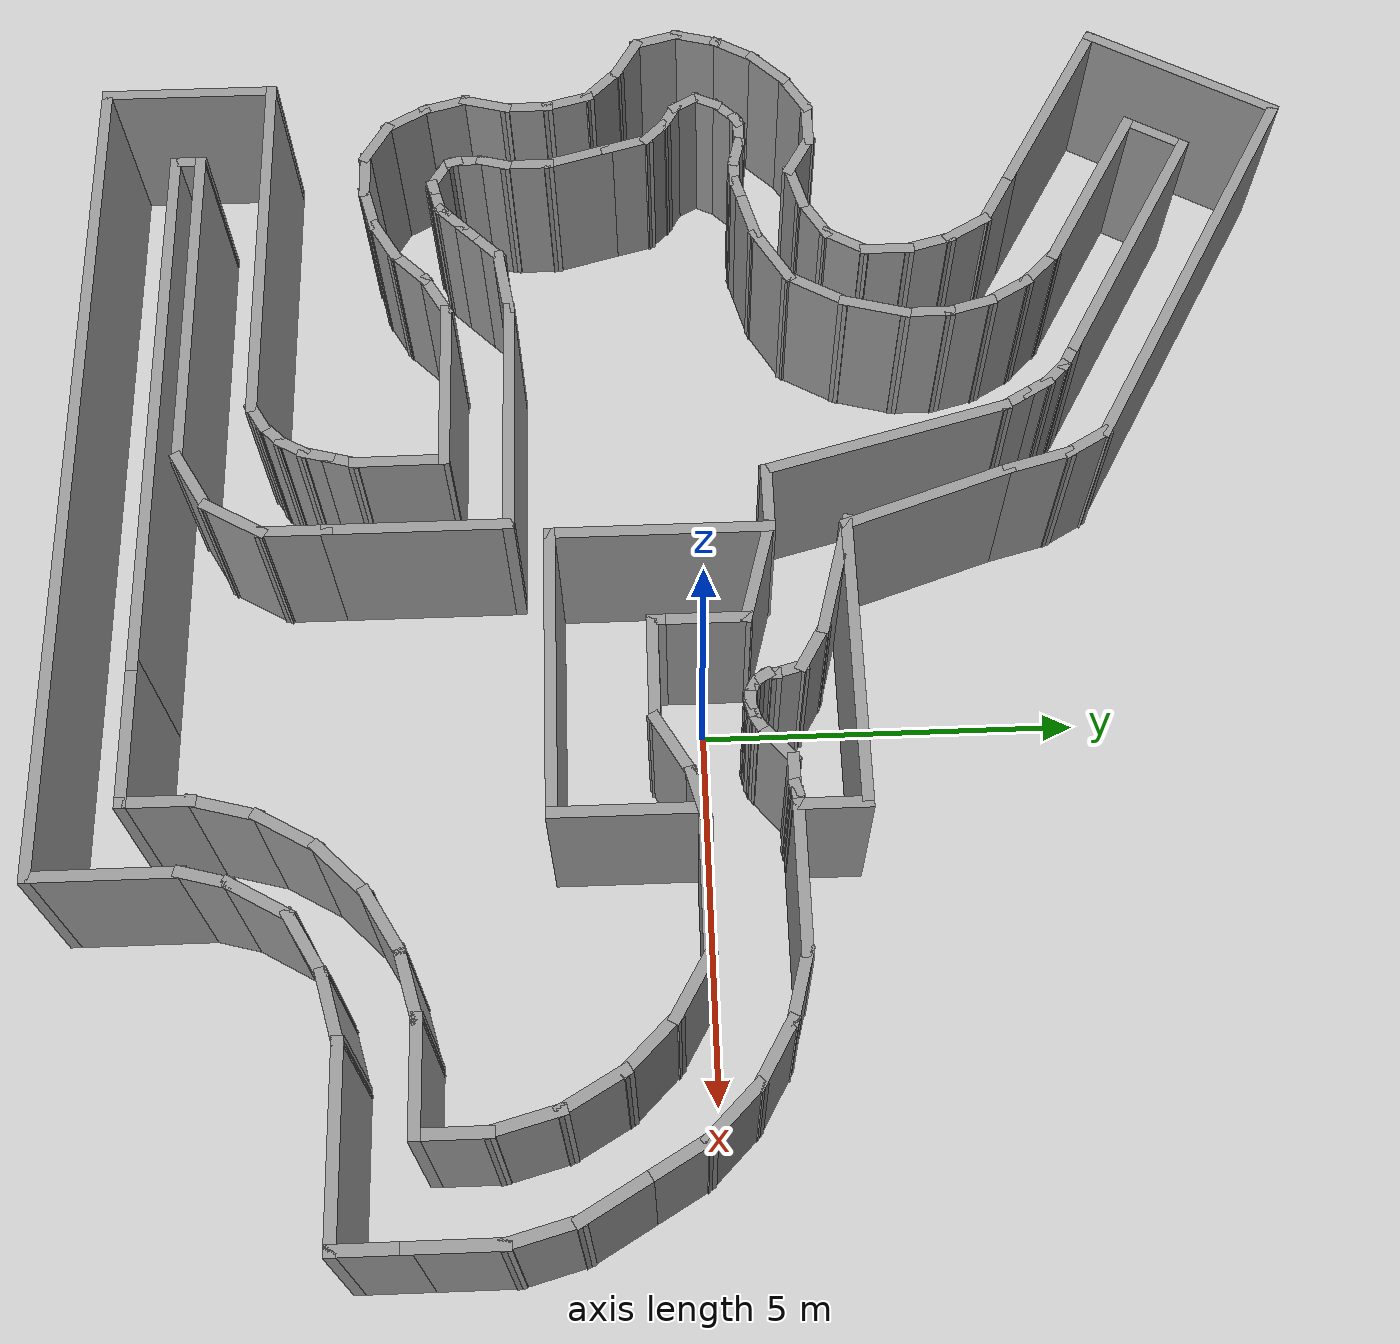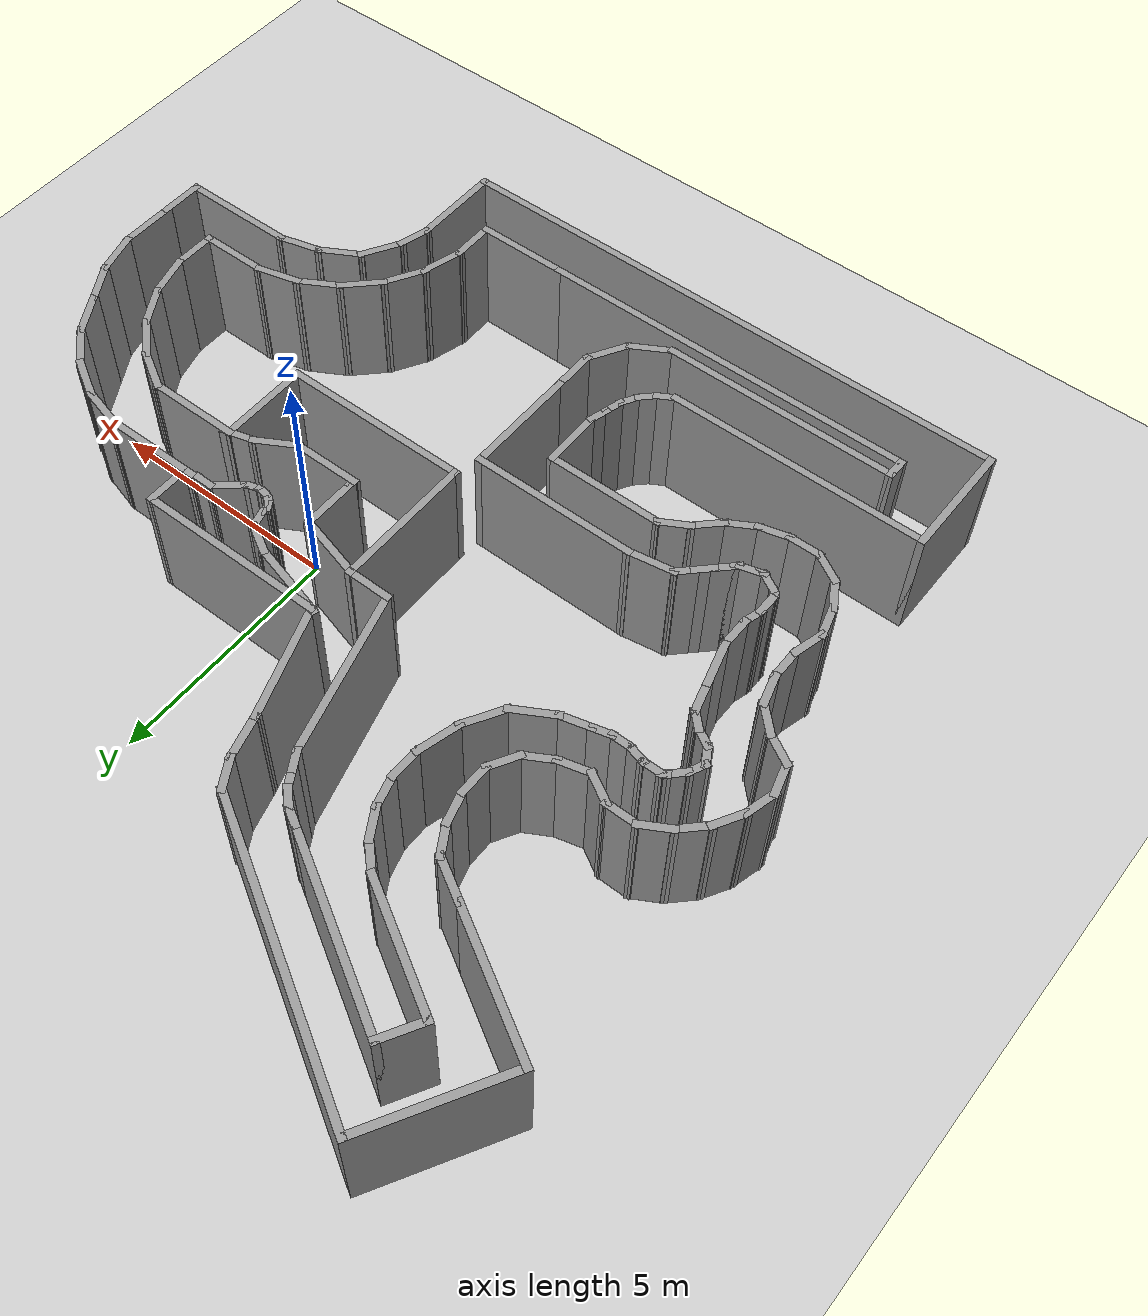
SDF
<sdf version="1.7">
 <world name="default">
  <light name="sun" type="directional">
   <pose>0 0 10 0 -0 0</pose>
   <diffuse>0.8 0.8 0.8 1</diffuse>
   <specular>0.2 0.2 0.2 1</specular>
   <attenuation>
    <range>1000</range>
    <constant>0.9</constant>
    <linear>0.01</linear>
    <quadratic>0.001</quadratic>
   </attenuation>
   <direction>-0.5 0.1 -0.9</direction>
   <spot><inner_angle>0</inner_angle><outer_angle>0</outer_angle><falloff>0</falloff></spot>
  </light>
  <model name="ground_plane">
   <static>1</static>
   <link name="link">
    <collision name="collision">
     <geometry><plane><normal>0 0 1</normal><size>100 100</size></plane></geometry>
     <surface><friction><ode><mu>100</mu><mu2>50</mu2></ode></friction></surface>
    </collision>
    <visual name="visual">
     <cast_shadows>0</cast_shadows>
     <geometry><plane><normal>0 0 1</normal><size>100 100</size></plane></geometry>
     <material>
      <script><uri>file://media/materials/scripts/gazebo.material</uri><name>Gazebo/Grey</name></script>
     </material>
    </visual>
   </link>
  </model>
  <gravity>0 0 -9.8</gravity>
  <magnetic_field>6e-06 2.3e-05 -4.2e-05</magnetic_field>
  <atmosphere type="adiabatic"/>
  <physics type="ode">
   <max_step_size>0.001</max_step_size>
   <real_time_factor>1</real_time_factor>
   <real_time_update_rate>1000</real_time_update_rate>
  </physics>
  <scene><ambient>0.4 0.4 0.4 1</ambient><background>0.7 0.7 0.7 1</background><shadows>1</shadows></scene>
  <audio><device>default</device></audio>
  <spherical_coordinates>
   <surface_model>EARTH_WGS84</surface_model>
   <latitude_deg>0</latitude_deg>
   <longitude_deg>0</longitude_deg>
   <elevation>0</elevation>
   <heading_deg>0</heading_deg>
  </spherical_coordinates>
  <model name="labirinth">
   <pose>-1.55942 0.15521 0 0 -0 0</pose>
   <link name="Wall_100">
    <collision name="Wall_100_Collision">
     <geometry><box><size>0.75 0.15 2.5</size></box></geometry>
     <pose>0 0 1.25 0 -0 0</pose>
    </collision>
    <visual name="Wall_100_Visual">
     <pose>0 0 1.25 0 -0 0</pose>
     <geometry><box><size>0.75 0.15 2.5</size></box></geometry>
     <material>
      <script><uri>file://media/materials/scripts/gazebo.material</uri><name>Gazebo/Grey</name></script>
      <ambient>1 1 1 1</ambient>
     </material>
     <meta><layer>0</layer></meta>
    </visual>
    <pose>-4.80966 2.0706 0 0 -0 1.0472</pose>
   </link>
   <link name="Wall_101">
    <collision name="Wall_101_Collision">
     <geometry><box><size>0.75 0.15 2.5</size></box></geometry>
     <pose>0 0 1.25 0 -0 0</pose>
    </collision>
    <visual name="Wall_101_Visual">
     <pose>0 0 1.25 0 -0 0</pose>
     <geometry><box><size>0.75 0.15 2.5</size></box></geometry>
     <material>
      <script><uri>file://media/materials/scripts/gazebo.material</uri><name>Gazebo/Grey</name></script>
      <ambient>1 1 1 1</ambient>
     </material>
     <meta><layer>0</layer></meta>
    </visual>
    <pose>-4.65966 2.6304 0 0 -0 1.5708</pose>
   </link>
   <link name="Wall_102">
    <collision name="Wall_102_Collision">
     <geometry><box><size>0.75 0.15 2.5</size></box></geometry>
     <pose>0 0 1.25 0 -0 0</pose>
    </collision>
    <visual name="Wall_102_Visual">
     <pose>0 0 1.25 0 -0 0</pose>
     <geometry><box><size>0.75 0.15 2.5</size></box></geometry>
     <material>
      <script><uri>file://media/materials/scripts/gazebo.material</uri><name>Gazebo/Grey</name></script>
      <ambient>1 1 1 1</ambient>
     </material>
     <meta><layer>0</layer></meta>
    </visual>
    <pose>-4.73731 3.22018 0 0 -0 1.8326</pose>
   </link>
   <link name="Wall_103">
    <collision name="Wall_103_Collision">
     <geometry><box><size>0.75 0.15 2.5</size></box></geometry>
     <pose>0 0 1.25 0 -0 0</pose>
    </collision>
    <visual name="Wall_103_Visual">
     <pose>0 0 1.25 0 -0 0</pose>
     <geometry><box><size>0.75 0.15 2.5</size></box></geometry>
     <material>
      <script><uri>file://media/materials/scripts/gazebo.material</uri><name>Gazebo/Grey</name></script>
      <ambient>1 1 1 1</ambient>
     </material>
     <meta><layer>0</layer></meta>
    </visual>
    <pose>-4.96495 3.76977 0 0 -0 2.0944</pose>
   </link>
   <link name="Wall_104">
    <collision name="Wall_104_Collision">
     <geometry><box><size>1 0.15 2.5</size></box></geometry>
     <pose>0 0 1.25 0 -0 0</pose>
    </collision>
    <visual name="Wall_104_Visual">
     <pose>0 0 1.25 0 -0 0</pose>
     <geometry><box><size>1 0.15 2.5</size></box></geometry>
     <material>
      <script><uri>file://media/materials/scripts/gazebo.material</uri><name>Gazebo/Grey</name></script>
      <ambient>1 1 1 1</ambient>
     </material>
     <meta><layer>0</layer></meta>
    </visual>
    <pose>-5.48301 4.24207 0 0 -0 2.61799</pose>
   </link>
   <link name="Wall_105">
    <collision name="Wall_105_Collision">
     <geometry><box><size>3 0.15 2.5</size></box></geometry>
     <pose>0 0 1.25 0 -0 0</pose>
    </collision>
    <visual name="Wall_105_Visual">
     <pose>0 0 1.25 0 -0 0</pose>
     <geometry><box><size>3 0.15 2.5</size></box></geometry>
     <material>
      <script><uri>file://media/materials/scripts/gazebo.material</uri><name>Gazebo/Grey</name></script>
      <ambient>1 1 1 1</ambient>
     </material>
     <meta><layer>0</layer></meta>
    </visual>
    <pose>-7.08516 5.16707 0 0 -0 2.61799</pose>
   </link>
   <link name="Wall_106">
    <collision name="Wall_106_Collision">
     <geometry><box><size>3 0.15 2.5</size></box></geometry>
     <pose>0 0 1.25 0 -0 0</pose>
    </collision>
    <visual name="Wall_106_Visual">
     <pose>0 0 1.25 0 -0 0</pose>
     <geometry><box><size>3 0.15 2.5</size></box></geometry>
     <material>
      <script><uri>file://media/materials/scripts/gazebo.material</uri><name>Gazebo/Grey</name></script>
      <ambient>1 1 1 1</ambient>
     </material>
     <meta><layer>0</layer></meta>
    </visual>
    <pose>-7.60675 7.11366 0 0 -0 1.0472</pose>
   </link>
   <link name="Wall_107">
    <collision name="Wall_107_Collision">
     <geometry><box><size>6.25 0.15 2.5</size></box></geometry>
     <pose>0 0 1.25 0 -0 0</pose>
    </collision>
    <visual name="Wall_107_Visual">
     <pose>0 0 1.25 0 -0 0</pose>
     <geometry><box><size>6.25 0.15 2.5</size></box></geometry>
     <material>
      <script><uri>file://media/materials/scripts/gazebo.material</uri><name>Gazebo/Grey</name></script>
      <ambient>1 1 1 1</ambient>
     </material>
     <meta><layer>0</layer></meta>
    </visual>
    <pose>-4.25287 6.82275 0 0 -0 -0.523599</pose>
   </link>
   <link name="Wall_108">
    <collision name="Wall_108_Collision">
     <geometry><box><size>0.75 0.15 2.5</size></box></geometry>
     <pose>0 0 1.25 0 -0 0</pose>
    </collision>
    <visual name="Wall_108_Visual">
     <pose>0 0 1.25 0 -0 0</pose>
     <geometry><box><size>0.75 0.15 2.5</size></box></geometry>
     <material>
      <script><uri>file://media/materials/scripts/gazebo.material</uri><name>Gazebo/Grey</name></script>
      <ambient>1 1 1 1</ambient>
     </material>
     <meta><layer>0</layer></meta>
    </visual>
    <pose>-1.46149 5.03794 0 0 -0 -1.0472</pose>
   </link>
   <link name="Wall_109">
    <collision name="Wall_109_Collision">
     <geometry><box><size>1 0.15 2.5</size></box></geometry>
     <pose>0 0 1.25 0 -0 0</pose>
    </collision>
    <visual name="Wall_109_Visual">
     <pose>0 0 1.25 0 -0 0</pose>
     <geometry><box><size>1 0.15 2.5</size></box></geometry>
     <material>
      <script><uri>file://media/materials/scripts/gazebo.material</uri><name>Gazebo/Grey</name></script>
      <ambient>1 1 1 1</ambient>
     </material>
     <meta><layer>0</layer></meta>
    </visual>
    <pose>-1.20149 4.36761 0 0 -0 -1.309</pose>
   </link>
   <link name="Wall_11">
    <collision name="Wall_11_Collision">
     <geometry><box><size>1 0.15 2.5</size></box></geometry>
     <pose>0 0 1.25 0 -0 0</pose>
    </collision>
    <visual name="Wall_11_Visual">
     <pose>0 0 1.25 0 -0 0</pose>
     <geometry><box><size>1 0.15 2.5</size></box></geometry>
     <material>
      <script><uri>file://media/materials/scripts/gazebo.material</uri><name>Gazebo/Grey</name></script>
      <ambient>1 1 1 1</ambient>
     </material>
     <meta><layer>0</layer></meta>
    </visual>
    <pose>5.71748 -0.43771 0 0 -0 -0.523599</pose>
   </link>
   <link name="Wall_110">
    <collision name="Wall_110_Collision">
     <geometry><box><size>2.45465 0.15 2.5</size></box></geometry>
     <pose>0 0 1.25 0 -0 0</pose>
    </collision>
    <visual name="Wall_110_Visual">
     <pose>0 0 1.25 0 -0 0</pose>
     <geometry><box><size>2.45465 0.15 2.5</size></box></geometry>
     <material>
      <script><uri>file://media/materials/scripts/gazebo.material</uri><name>Gazebo/Grey</name></script>
      <ambient>1 1 1 1</ambient>
     </material>
     <meta><layer>0</layer></meta>
    </visual>
    <pose>-0.721037 2.86594 0 0 -0 -1.2435</pose>
   </link>
   <link name="Wall_112">
    <collision name="Wall_112_Collision">
     <geometry><box><size>3 0.15 2.5</size></box></geometry>
     <pose>0 0 1.25 0 -0 0</pose>
    </collision>
    <visual name="Wall_112_Visual">
     <pose>0 0 1.25 0 -0 0</pose>
     <geometry><box><size>3 0.15 2.5</size></box></geometry>
     <material>
      <script><uri>file://media/materials/scripts/gazebo.material</uri><name>Gazebo/Grey</name></script>
      <ambient>1 1 1 1</ambient>
     </material>
     <meta><layer>0</layer></meta>
    </visual>
    <pose>-0.350577 -0.65021 0 0 -0 1.5708</pose>
   </link>
   <link name="Wall_113">
    <collision name="Wall_113_Collision">
     <geometry><box><size>1 0.15 2.5</size></box></geometry>
     <pose>0 0 1.25 0 -0 0</pose>
    </collision>
    <visual name="Wall_113_Visual">
     <pose>0 0 1.25 0 -0 0</pose>
     <geometry><box><size>1 0.15 2.5</size></box></geometry>
     <material>
      <script><uri>file://media/materials/scripts/gazebo.material</uri><name>Gazebo/Grey</name></script>
      <ambient>1 1 1 1</ambient>
     </material>
     <meta><layer>0</layer></meta>
    </visual>
    <pose>-0.775577 0.77479 0 0 -0 3.14159</pose>
   </link>
   <link name="Wall_114">
    <collision name="Wall_114_Collision">
     <geometry><box><size>3.5 0.15 2.5</size></box></geometry>
     <pose>0 0 1.25 0 -0 0</pose>
    </collision>
    <visual name="Wall_114_Visual">
     <pose>0 0 1.25 0 -0 0</pose>
     <geometry><box><size>3.5 0.15 2.5</size></box></geometry>
     <material>
      <script><uri>file://media/materials/scripts/gazebo.material</uri><name>Gazebo/Grey</name></script>
      <ambient>1 1 1 1</ambient>
     </material>
     <meta><layer>0</layer></meta>
    </visual>
    <pose>-1.6341 2.39272 0 0 -0 1.8326</pose>
   </link>
   <link name="Wall_115">
    <collision name="Wall_115_Collision">
     <geometry><box><size>0.5 0.15 2.5</size></box></geometry>
     <pose>0 0 1.25 0 -0 0</pose>
    </collision>
    <visual name="Wall_115_Visual">
     <pose>0 0 1.25 0 -0 0</pose>
     <geometry><box><size>0.5 0.15 2.5</size></box></geometry>
     <material>
      <script><uri>file://media/materials/scripts/gazebo.material</uri><name>Gazebo/Grey</name></script>
      <ambient>1 1 1 1</ambient>
     </material>
     <meta><layer>0</layer></meta>
    </visual>
    <pose>-2.15512 4.1622 0 0 -0 2.0944</pose>
   </link>
   <link name="Wall_116">
    <collision name="Wall_116_Collision">
     <geometry><box><size>0.5 0.15 2.5</size></box></geometry>
     <pose>0 0 1.25 0 -0 0</pose>
    </collision>
    <visual name="Wall_116_Visual">
     <pose>0 0 1.25 0 -0 0</pose>
     <geometry><box><size>0.5 0.15 2.5</size></box></geometry>
     <material>
      <script><uri>file://media/materials/scripts/gazebo.material</uri><name>Gazebo/Grey</name></script>
      <ambient>1 1 1 1</ambient>
     </material>
     <meta><layer>0</layer></meta>
    </visual>
    <pose>-2.33012 4.4653 0 0 -0 2.0944</pose>
   </link>
   <link name="Wall_117">
    <collision name="Wall_117_Collision">
     <geometry><box><size>0.5 0.15 2.5</size></box></geometry>
     <pose>0 0 1.25 0 -0 0</pose>
    </collision>
    <visual name="Wall_117_Visual">
     <pose>0 0 1.25 0 -0 0</pose>
     <geometry><box><size>0.5 0.15 2.5</size></box></geometry>
     <material>
      <script><uri>file://media/materials/scripts/gazebo.material</uri><name>Gazebo/Grey</name></script>
      <ambient>1 1 1 1</ambient>
     </material>
     <meta><layer>0</layer></meta>
    </visual>
    <pose>-2.54136 4.7406 0 0 -0 2.35619</pose>
   </link>
   <link name="Wall_118">
    <collision name="Wall_118_Collision">
     <geometry><box><size>0.5 0.15 2.5</size></box></geometry>
     <pose>0 0 1.25 0 -0 0</pose>
    </collision>
    <visual name="Wall_118_Visual">
     <pose>0 0 1.25 0 -0 0</pose>
     <geometry><box><size>0.5 0.15 2.5</size></box></geometry>
     <material>
      <script><uri>file://media/materials/scripts/gazebo.material</uri><name>Gazebo/Grey</name></script>
      <ambient>1 1 1 1</ambient>
     </material>
     <meta><layer>0</layer></meta>
    </visual>
    <pose>-2.81666 4.95185 0 0 -0 2.61799</pose>
   </link>
   <link name="Wall_119">
    <collision name="Wall_119_Collision">
     <geometry><box><size>4 0.15 2.5</size></box></geometry>
     <pose>0 0 1.25 0 -0 0</pose>
    </collision>
    <visual name="Wall_119_Visual">
     <pose>0 0 1.25 0 -0 0</pose>
     <geometry><box><size>4 0.15 2.5</size></box></geometry>
     <material>
      <script><uri>file://media/materials/scripts/gazebo.material</uri><name>Gazebo/Grey</name></script>
      <ambient>1 1 1 1</ambient>
     </material>
     <meta><layer>0</layer></meta>
    </visual>
    <pose>-4.63532 6.00185 0 0 -0 2.61799</pose>
   </link>
   <link name="Wall_12">
    <collision name="Wall_12_Collision">
     <geometry><box><size>1 0.15 2.5</size></box></geometry>
     <pose>0 0 1.25 0 -0 0</pose>
    </collision>
    <visual name="Wall_12_Visual">
     <pose>0 0 1.25 0 -0 0</pose>
     <geometry><box><size>1 0.15 2.5</size></box></geometry>
     <material>
      <script><uri>file://media/materials/scripts/gazebo.material</uri><name>Gazebo/Grey</name></script>
      <ambient>1 1 1 1</ambient>
     </material>
     <meta><layer>0</layer></meta>
    </visual>
    <pose>6.38607 -0.95073 0 0 -0 -0.785398</pose>
   </link>
   <link name="Wall_120">
    <collision name="Wall_120_Collision">
     <geometry><box><size>1 0.15 2.5</size></box></geometry>
     <pose>0 0 1.25 0 -0 0</pose>
    </collision>
    <visual name="Wall_120_Visual">
     <pose>0 0 1.25 0 -0 0</pose>
     <geometry><box><size>1 0.15 2.5</size></box></geometry>
     <material>
      <script><uri>file://media/materials/scripts/gazebo.material</uri><name>Gazebo/Grey</name></script>
      <ambient>1 1 1 1</ambient>
     </material>
     <meta><layer>0</layer></meta>
    </visual>
    <pose>-6.51492 6.59629 0 0 -0 -2.0944</pose>
   </link>
   <link name="Wall_121">
    <collision name="Wall_121_Collision">
     <geometry><box><size>2.75 0.15 2.5</size></box></geometry>
     <pose>0 0 1.25 0 -0 0</pose>
    </collision>
    <visual name="Wall_121_Visual">
     <pose>0 0 1.25 0 -0 0</pose>
     <geometry><box><size>2.75 0.15 2.5</size></box></geometry>
     <material>
      <script><uri>file://media/materials/scripts/gazebo.material</uri><name>Gazebo/Grey</name></script>
      <ambient>1 1 1 1</ambient>
     </material>
     <meta><layer>0</layer></meta>
    </visual>
    <pose>-5.60158 5.57823 0 0 -0 -0.523599</pose>
   </link>
   <link name="Wall_122">
    <collision name="Wall_122_Collision">
     <geometry><box><size>0.75 0.15 2.5</size></box></geometry>
     <pose>0 0 1.25 0 -0 0</pose>
    </collision>
    <visual name="Wall_122_Visual">
     <pose>0 0 1.25 0 -0 0</pose>
     <geometry><box><size>0.75 0.15 2.5</size></box></geometry>
     <material>
      <script><uri>file://media/materials/scripts/gazebo.material</uri><name>Gazebo/Grey</name></script>
      <ambient>1 1 1 1</ambient>
     </material>
     <meta><layer>0</layer></meta>
    </visual>
    <pose>-4.26362 4.71609 0 0 -0 -0.785398</pose>
   </link>
   <link name="Wall_123">
    <collision name="Wall_123_Collision">
     <geometry><box><size>0.75 0.15 2.5</size></box></geometry>
     <pose>0 0 1.25 0 -0 0</pose>
    </collision>
    <visual name="Wall_123_Visual">
     <pose>0 0 1.25 0 -0 0</pose>
     <geometry><box><size>0.75 0.15 2.5</size></box></geometry>
     <material>
      <script><uri>file://media/materials/scripts/gazebo.material</uri><name>Gazebo/Grey</name></script>
      <ambient>1 1 1 1</ambient>
     </material>
     <meta><layer>0</layer></meta>
    </visual>
    <pose>-3.90148 4.24415 0 0 -0 -1.0472</pose>
   </link>
   <link name="Wall_124">
    <collision name="Wall_124_Collision">
     <geometry><box><size>0.75 0.15 2.5</size></box></geometry>
     <pose>0 0 1.25 0 -0 0</pose>
    </collision>
    <visual name="Wall_124_Visual">
     <pose>0 0 1.25 0 -0 0</pose>
     <geometry><box><size>0.75 0.15 2.5</size></box></geometry>
     <material>
      <script><uri>file://media/materials/scripts/gazebo.material</uri><name>Gazebo/Grey</name></script>
      <ambient>1 1 1 1</ambient>
     </material>
     <meta><layer>0</layer></meta>
    </visual>
    <pose>-3.67384 3.69457 0 0 -0 -1.309</pose>
   </link>
   <link name="Wall_125">
    <collision name="Wall_125_Collision">
     <geometry><box><size>0.75 0.15 2.5</size></box></geometry>
     <pose>0 0 1.25 0 -0 0</pose>
    </collision>
    <visual name="Wall_125_Visual">
     <pose>0 0 1.25 0 -0 0</pose>
     <geometry><box><size>0.75 0.15 2.5</size></box></geometry>
     <material>
      <script><uri>file://media/materials/scripts/gazebo.material</uri><name>Gazebo/Grey</name></script>
      <ambient>1 1 1 1</ambient>
     </material>
     <meta><layer>0</layer></meta>
    </visual>
    <pose>-3.59619 3.10479 0 0 -0 -1.5708</pose>
   </link>
   <link name="Wall_126">
    <collision name="Wall_126_Collision">
     <geometry><box><size>1 0.15 2.5</size></box></geometry>
     <pose>0 0 1.25 0 -0 0</pose>
    </collision>
    <visual name="Wall_126_Visual">
     <pose>0 0 1.25 0 -0 0</pose>
     <geometry><box><size>1 0.15 2.5</size></box></geometry>
     <material>
      <script><uri>file://media/materials/scripts/gazebo.material</uri><name>Gazebo/Grey</name></script>
      <ambient>1 1 1 1</ambient>
     </material>
     <meta><layer>0</layer></meta>
    </visual>
    <pose>-3.70619 2.39427 0 0 -0 -1.8326</pose>
   </link>
   <link name="Wall_127">
    <collision name="Wall_127_Collision">
     <geometry><box><size>1 0.15 2.5</size></box></geometry>
     <pose>0 0 1.25 0 -0 0</pose>
    </collision>
    <visual name="Wall_127_Visual">
     <pose>0 0 1.25 0 -0 0</pose>
     <geometry><box><size>1 0.15 2.5</size></box></geometry>
     <material>
      <script><uri>file://media/materials/scripts/gazebo.material</uri><name>Gazebo/Grey</name></script>
      <ambient>1 1 1 1</ambient>
     </material>
     <meta><layer>0</layer></meta>
    </visual>
    <pose>-4.02869 1.61569 0 0 -0 -2.0944</pose>
   </link>
   <link name="Wall_128">
    <collision name="Wall_128_Collision">
     <geometry><box><size>1 0.15 2.5</size></box></geometry>
     <pose>0 0 1.25 0 -0 0</pose>
    </collision>
    <visual name="Wall_128_Visual">
     <pose>0 0 1.25 0 -0 0</pose>
     <geometry><box><size>1 0.15 2.5</size></box></geometry>
     <material>
      <script><uri>file://media/materials/scripts/gazebo.material</uri><name>Gazebo/Grey</name></script>
      <ambient>1 1 1 1</ambient>
     </material>
     <meta><layer>0</layer></meta>
    </visual>
    <pose>-4.60925 1.03513 0 0 -0 -2.61799</pose>
   </link>
   <link name="Wall_129">
    <collision name="Wall_129_Collision">
     <geometry><box><size>0.75 0.15 2.5</size></box></geometry>
     <pose>0 0 1.25 0 -0 0</pose>
    </collision>
    <visual name="Wall_129_Visual">
     <pose>0 0 1.25 0 -0 0</pose>
     <geometry><box><size>0.75 0.15 2.5</size></box></geometry>
     <material>
      <script><uri>file://media/materials/scripts/gazebo.material</uri><name>Gazebo/Grey</name></script>
      <ambient>1 1 1 1</ambient>
     </material>
     <meta><layer>0</layer></meta>
    </visual>
    <pose>-5.26709 0.744986 0 0 -0 -2.87979</pose>
   </link>
   <link name="Wall_13">
    <collision name="Wall_13_Collision">
     <geometry><box><size>1 0.15 2.5</size></box></geometry>
     <pose>0 0 1.25 0 -0 0</pose>
    </collision>
    <visual name="Wall_13_Visual">
     <pose>0 0 1.25 0 -0 0</pose>
     <geometry><box><size>1 0.15 2.5</size></box></geometry>
     <material>
      <script><uri>file://media/materials/scripts/gazebo.material</uri><name>Gazebo/Grey</name></script>
      <ambient>1 1 1 1</ambient>
     </material>
     <meta><layer>0</layer></meta>
    </visual>
    <pose>6.89909 -1.61931 0 0 -0 -1.0472</pose>
   </link>
   <link name="Wall_130">
    <collision name="Wall_130_Collision">
     <geometry><box><size>0.5 0.15 2.5</size></box></geometry>
     <pose>0 0 1.25 0 -0 0</pose>
    </collision>
    <visual name="Wall_130_Visual">
     <pose>0 0 1.25 0 -0 0</pose>
     <geometry><box><size>0.5 0.15 2.5</size></box></geometry>
     <material>
      <script><uri>file://media/materials/scripts/gazebo.material</uri><name>Gazebo/Grey</name></script>
      <ambient>1 1 1 1</ambient>
     </material>
     <meta><layer>0</layer></meta>
    </visual>
    <pose>-5.7259 0.622047 0 0 -0 -2.87979</pose>
   </link>
   <link name="Wall_132">
    <collision name="Wall_132_Collision">
     <geometry><box><size>0.5 0.15 2.5</size></box></geometry>
     <pose>0 0 1.25 0 -0 0</pose>
    </collision>
    <visual name="Wall_132_Visual">
     <pose>0 0 1.25 0 -0 0</pose>
     <geometry><box><size>0.5 0.15 2.5</size></box></geometry>
     <material>
      <script><uri>file://media/materials/scripts/gazebo.material</uri><name>Gazebo/Grey</name></script>
      <ambient>1 1 1 1</ambient>
     </material>
     <meta><layer>0</layer></meta>
    </visual>
    <pose>-6.06994 0.576754 0 0 -0 3.14159</pose>
   </link>
   <link name="Wall_133">
    <collision name="Wall_133_Collision">
     <geometry><box><size>0.5 0.15 2.5</size></box></geometry>
     <pose>0 0 1.25 0 -0 0</pose>
    </collision>
    <visual name="Wall_133_Visual">
     <pose>0 0 1.25 0 -0 0</pose>
     <geometry><box><size>0.5 0.15 2.5</size></box></geometry>
     <material>
      <script><uri>file://media/materials/scripts/gazebo.material</uri><name>Gazebo/Grey</name></script>
      <ambient>1 1 1 1</ambient>
     </material>
     <meta><layer>0</layer></meta>
    </visual>
    <pose>-6.41398 0.622047 0 0 -0 2.87979</pose>
   </link>
   <link name="Wall_134">
    <collision name="Wall_134_Collision">
     <geometry><box><size>0.5 0.15 2.5</size></box></geometry>
     <pose>0 0 1.25 0 -0 0</pose>
    </collision>
    <visual name="Wall_134_Visual">
     <pose>0 0 1.25 0 -0 0</pose>
     <geometry><box><size>0.5 0.15 2.5</size></box></geometry>
     <material>
      <script><uri>file://media/materials/scripts/gazebo.material</uri><name>Gazebo/Grey</name></script>
      <ambient>1 1 1 1</ambient>
     </material>
     <meta><layer>0</layer></meta>
    </visual>
    <pose>-6.75802 0.667341 0 0 -0 3.14159</pose>
   </link>
   <link name="Wall_135">
    <collision name="Wall_135_Collision">
     <geometry><box><size>0.25 0.15 2.5</size></box></geometry>
     <pose>0 0 1.25 0 -0 0</pose>
    </collision>
    <visual name="Wall_135_Visual">
     <pose>0 0 1.25 0 -0 0</pose>
     <geometry><box><size>0.25 0.15 2.5</size></box></geometry>
     <material>
      <script><uri>file://media/materials/scripts/gazebo.material</uri><name>Gazebo/Grey</name></script>
      <ambient>1 1 1 1</ambient>
     </material>
     <meta><layer>0</layer></meta>
    </visual>
    <pose>-6.97631 0.642341 0 0 -0 -2.61799</pose>
   </link>
   <link name="Wall_136">
    <collision name="Wall_136_Collision">
     <geometry><box><size>0.5 0.15 2.5</size></box></geometry>
     <pose>0 0 1.25 0 -0 0</pose>
    </collision>
    <visual name="Wall_136_Visual">
     <pose>0 0 1.25 0 -0 0</pose>
     <geometry><box><size>0.5 0.15 2.5</size></box></geometry>
     <material>
      <script><uri>file://media/materials/scripts/gazebo.material</uri><name>Gazebo/Grey</name></script>
      <ambient>1 1 1 1</ambient>
     </material>
     <meta><layer>0</layer></meta>
    </visual>
    <pose>-7.14336 0.493597 0 0 -0 -2.35619</pose>
   </link>
   <link name="Wall_137">
    <collision name="Wall_137_Collision">
     <geometry><box><size>0.469915 0.15 2.5</size></box></geometry>
     <pose>0 0 1.25 0 -0 0</pose>
    </collision>
    <visual name="Wall_137_Visual">
     <pose>0 0 1.25 0 -0 0</pose>
     <geometry><box><size>0.469915 0.15 2.5</size></box></geometry>
     <material>
      <script><uri>file://media/materials/scripts/gazebo.material</uri><name>Gazebo/Grey</name></script>
      <ambient>1 1 1 1</ambient>
     </material>
     <meta><layer>0</layer></meta>
    </visual>
    <pose>-7.33477 0.224911 0 0 -0 -2.00755</pose>
   </link>
   <link name="Wall_14">
    <collision name="Wall_14_Collision">
     <geometry><box><size>1 0.15 2.5</size></box></geometry>
     <pose>0 0 1.25 0 -0 0</pose>
    </collision>
    <visual name="Wall_14_Visual">
     <pose>0 0 1.25 0 -0 0</pose>
     <geometry><box><size>1 0.15 2.5</size></box></geometry>
     <material>
      <script><uri>file://media/materials/scripts/gazebo.material</uri><name>Gazebo/Grey</name></script>
      <ambient>1 1 1 1</ambient>
     </material>
     <meta><layer>0</layer></meta>
    </visual>
    <pose>7.22158 -2.39789 0 0 -0 -1.309</pose>
   </link>
   <link name="Wall_140">
    <collision name="Wall_140_Collision">
     <geometry><box><size>0.5 0.15 2.5</size></box></geometry>
     <pose>0 0 1.25 0 -0 0</pose>
    </collision>
    <visual name="Wall_140_Visual">
     <pose>0 0 1.25 0 -0 0</pose>
     <geometry><box><size>0.5 0.15 2.5</size></box></geometry>
     <material>
      <script><uri>file://media/materials/scripts/gazebo.material</uri><name>Gazebo/Grey</name></script>
      <ambient>1 1 1 1</ambient>
     </material>
     <meta><layer>0</layer></meta>
    </visual>
    <pose>-7.31493 -0.071585 0 0 -0 -1.0472</pose>
   </link>
   <link name="Wall_141">
    <collision name="Wall_141_Collision">
     <geometry><box><size>0.5 0.15 2.5</size></box></geometry>
     <pose>0 0 1.25 0 -0 0</pose>
    </collision>
    <visual name="Wall_141_Visual">
     <pose>0 0 1.25 0 -0 0</pose>
     <geometry><box><size>0.5 0.15 2.5</size></box></geometry>
     <material>
      <script><uri>file://media/materials/scripts/gazebo.material</uri><name>Gazebo/Grey</name></script>
      <ambient>1 1 1 1</ambient>
     </material>
     <meta><layer>0</layer></meta>
    </visual>
    <pose>-7.07587 -0.310639 0 0 -0 -0.523599</pose>
   </link>
   <link name="Wall_142">
    <collision name="Wall_142_Collision">
     <geometry><box><size>0.5 0.15 2.5</size></box></geometry>
     <pose>0 0 1.25 0 -0 0</pose>
    </collision>
    <visual name="Wall_142_Visual">
     <pose>0 0 1.25 0 -0 0</pose>
     <geometry><box><size>0.5 0.15 2.5</size></box></geometry>
     <material>
      <script><uri>file://media/materials/scripts/gazebo.material</uri><name>Gazebo/Grey</name></script>
      <ambient>1 1 1 1</ambient>
     </material>
     <meta><layer>0</layer></meta>
    </visual>
    <pose>-6.80058 -0.521883 0 0 -0 -0.785398</pose>
   </link>
   <link name="Wall_143">
    <collision name="Wall_143_Collision">
     <geometry><box><size>0.75 0.15 2.5</size></box></geometry>
     <pose>0 0 1.25 0 -0 0</pose>
    </collision>
    <visual name="Wall_143_Visual">
     <pose>0 0 1.25 0 -0 0</pose>
     <geometry><box><size>0.75 0.15 2.5</size></box></geometry>
     <material>
      <script><uri>file://media/materials/scripts/gazebo.material</uri><name>Gazebo/Grey</name></script>
      <ambient>1 1 1 1</ambient>
     </material>
     <meta><layer>0</layer></meta>
    </visual>
    <pose>-6.59919 -0.935405 0 0 -0 -1.309</pose>
   </link>
   <link name="Wall_144">
    <collision name="Wall_144_Collision">
     <geometry><box><size>1 0.15 2.5</size></box></geometry>
     <pose>0 0 1.25 0 -0 0</pose>
    </collision>
    <visual name="Wall_144_Visual">
     <pose>0 0 1.25 0 -0 0</pose>
     <geometry><box><size>1 0.15 2.5</size></box></geometry>
     <material>
      <script><uri>file://media/materials/scripts/gazebo.material</uri><name>Gazebo/Grey</name></script>
      <ambient>1 1 1 1</ambient>
     </material>
     <meta><layer>0</layer></meta>
    </visual>
    <pose>-6.41154 -1.6357 0 0 -0 -1.309</pose>
   </link>
   <link name="Wall_145">
    <collision name="Wall_145_Collision">
     <geometry><box><size>0.75 0.15 2.5</size></box></geometry>
     <pose>0 0 1.25 0 -0 0</pose>
    </collision>
    <visual name="Wall_145_Visual">
     <pose>0 0 1.25 0 -0 0</pose>
     <geometry><box><size>0.75 0.15 2.5</size></box></geometry>
     <material>
      <script><uri>file://media/materials/scripts/gazebo.material</uri><name>Gazebo/Grey</name></script>
      <ambient>1 1 1 1</ambient>
     </material>
     <meta><layer>0</layer></meta>
    </visual>
    <pose>-6.30154 -2.34622 0 0 -0 -1.5708</pose>
   </link>
   <link name="Wall_146">
    <collision name="Wall_146_Collision">
     <geometry><box><size>0.5 0.15 2.5</size></box></geometry>
     <pose>0 0 1.25 0 -0 0</pose>
    </collision>
    <visual name="Wall_146_Visual">
     <pose>0 0 1.25 0 -0 0</pose>
     <geometry><box><size>0.5 0.15 2.5</size></box></geometry>
     <material>
      <script><uri>file://media/materials/scripts/gazebo.material</uri><name>Gazebo/Grey</name></script>
      <ambient>1 1 1 1</ambient>
     </material>
     <meta><layer>0</layer></meta>
    </visual>
    <pose>-6.34684 -2.81526 0 0 -0 -1.8326</pose>
   </link>
   <link name="Wall_147">
    <collision name="Wall_147_Collision">
     <geometry><box><size>0.5 0.15 2.5</size></box></geometry>
     <pose>0 0 1.25 0 -0 0</pose>
    </collision>
    <visual name="Wall_147_Visual">
     <pose>0 0 1.25 0 -0 0</pose>
     <geometry><box><size>0.5 0.15 2.5</size></box></geometry>
     <material>
      <script><uri>file://media/materials/scripts/gazebo.material</uri><name>Gazebo/Grey</name></script>
      <ambient>1 1 1 1</ambient>
     </material>
     <meta><layer>0</layer></meta>
    </visual>
    <pose>-6.39213 -3.15929 0 0 -0 -1.5708</pose>
   </link>
   <link name="Wall_148">
    <collision name="Wall_148_Collision">
     <geometry><box><size>0.25 0.15 2.5</size></box></geometry>
     <pose>0 0 1.25 0 -0 0</pose>
    </collision>
    <visual name="Wall_148_Visual">
     <pose>0 0 1.25 0 -0 0</pose>
     <geometry><box><size>0.25 0.15 2.5</size></box></geometry>
     <material>
      <script><uri>file://media/materials/scripts/gazebo.material</uri><name>Gazebo/Grey</name></script>
      <ambient>1 1 1 1</ambient>
     </material>
     <meta><layer>0</layer></meta>
    </visual>
    <pose>-6.37919 -3.38259 0 0 -0 -1.309</pose>
   </link>
   <link name="Wall_149">
    <collision name="Wall_149_Collision">
     <geometry><box><size>0.25 0.15 2.5</size></box></geometry>
     <pose>0 0 1.25 0 -0 0</pose>
    </collision>
    <visual name="Wall_149_Visual">
     <pose>0 0 1.25 0 -0 0</pose>
     <geometry><box><size>0.25 0.15 2.5</size></box></geometry>
     <material>
      <script><uri>file://media/materials/scripts/gazebo.material</uri><name>Gazebo/Grey</name></script>
      <ambient>1 1 1 1</ambient>
     </material>
     <meta><layer>0</layer></meta>
    </visual>
    <pose>-6.33089 -3.46624 0 0 -0 -0.785398</pose>
   </link>
   <link name="Wall_15">
    <collision name="Wall_15_Collision">
     <geometry><box><size>1 0.15 2.5</size></box></geometry>
     <pose>0 0 1.25 0 -0 0</pose>
    </collision>
    <visual name="Wall_15_Visual">
     <pose>0 0 1.25 0 -0 0</pose>
     <geometry><box><size>1 0.15 2.5</size></box></geometry>
     <material>
      <script><uri>file://media/materials/scripts/gazebo.material</uri><name>Gazebo/Grey</name></script>
      <ambient>1 1 1 1</ambient>
     </material>
     <meta><layer>0</layer></meta>
    </visual>
    <pose>7.33158 -3.23341 0 0 -0 -1.5708</pose>
   </link>
   <link name="Wall_150">
    <collision name="Wall_150_Collision">
     <geometry><box><size>0.5 0.15 2.5</size></box></geometry>
     <pose>0 0 1.25 0 -0 0</pose>
    </collision>
    <visual name="Wall_150_Visual">
     <pose>0 0 1.25 0 -0 0</pose>
     <geometry><box><size>0.5 0.15 2.5</size></box></geometry>
     <material>
      <script><uri>file://media/materials/scripts/gazebo.material</uri><name>Gazebo/Grey</name></script>
      <ambient>1 1 1 1</ambient>
     </material>
     <meta><layer>0</layer></meta>
    </visual>
    <pose>-6.14398 -3.5891 0 0 -0 -0.523599</pose>
   </link>
   <link name="Wall_151">
    <collision name="Wall_151_Collision">
     <geometry><box><size>0.15 0.15 2.5</size></box></geometry>
     <pose>0 0 1.25 0 -0 0</pose>
    </collision>
    <visual name="Wall_151_Visual">
     <pose>0 0 1.25 0 -0 0</pose>
     <geometry><box><size>0.15 0.15 2.5</size></box></geometry>
     <material>
      <script><uri>file://media/materials/scripts/gazebo.material</uri><name>Gazebo/Grey</name></script>
      <ambient>1 1 1 1</ambient>
     </material>
     <meta><layer>0</layer></meta>
    </visual>
    <pose>-5.99243 -3.6766 0 0 -0 0</pose>
   </link>
   <link name="Wall_152">
    <collision name="Wall_152_Collision">
     <geometry><box><size>0.25 0.15 2.5</size></box></geometry>
     <pose>0 0 1.25 0 -0 0</pose>
    </collision>
    <visual name="Wall_152_Visual">
     <pose>0 0 1.25 0 -0 0</pose>
     <geometry><box><size>0.25 0.15 2.5</size></box></geometry>
     <material>
      <script><uri>file://media/materials/scripts/gazebo.material</uri><name>Gazebo/Grey</name></script>
      <ambient>1 1 1 1</ambient>
     </material>
     <meta><layer>0</layer></meta>
    </visual>
    <pose>-5.94413 -3.66366 0 0 -0 0.261799</pose>
   </link>
   <link name="Wall_153">
    <collision name="Wall_153_Collision">
     <geometry><box><size>0.5 0.15 2.5</size></box></geometry>
     <pose>0 0 1.25 0 -0 0</pose>
    </collision>
    <visual name="Wall_153_Visual">
     <pose>0 0 1.25 0 -0 0</pose>
     <geometry><box><size>0.5 0.15 2.5</size></box></geometry>
     <material>
      <script><uri>file://media/materials/scripts/gazebo.material</uri><name>Gazebo/Grey</name></script>
      <ambient>1 1 1 1</ambient>
     </material>
     <meta><layer>0</layer></meta>
    </visual>
    <pose>-5.7268 -3.60542 0 0 -0 0.261799</pose>
   </link>
   <link name="Wall_154">
    <collision name="Wall_154_Collision">
     <geometry><box><size>0.25 0.15 2.5</size></box></geometry>
     <pose>0 0 1.25 0 -0 0</pose>
    </collision>
    <visual name="Wall_154_Visual">
     <pose>0 0 1.25 0 -0 0</pose>
     <geometry><box><size>0.25 0.15 2.5</size></box></geometry>
     <material>
      <script><uri>file://media/materials/scripts/gazebo.material</uri><name>Gazebo/Grey</name></script>
      <ambient>1 1 1 1</ambient>
     </material>
     <meta><layer>0</layer></meta>
    </visual>
    <pose>-5.52241 -3.52477 0 0 -0 0.785398</pose>
   </link>
   <link name="Wall_155">
    <collision name="Wall_155_Collision">
     <geometry><box><size>0.5 0.15 2.5</size></box></geometry>
     <pose>0 0 1.25 0 -0 0</pose>
    </collision>
    <visual name="Wall_155_Visual">
     <pose>0 0 1.25 0 -0 0</pose>
     <geometry><box><size>0.5 0.15 2.5</size></box></geometry>
     <material>
      <script><uri>file://media/materials/scripts/gazebo.material</uri><name>Gazebo/Grey</name></script>
      <ambient>1 1 1 1</ambient>
     </material>
     <meta><layer>0</layer></meta>
    </visual>
    <pose>-5.36331 -3.36567 0 0 -0 0.785398</pose>
   </link>
   <link name="Wall_156">
    <collision name="Wall_156_Collision">
     <geometry><box><size>0.5 0.15 2.5</size></box></geometry>
     <pose>0 0 1.25 0 -0 0</pose>
    </collision>
    <visual name="Wall_156_Visual">
     <pose>0 0 1.25 0 -0 0</pose>
     <geometry><box><size>0.5 0.15 2.5</size></box></geometry>
     <material>
      <script><uri>file://media/materials/scripts/gazebo.material</uri><name>Gazebo/Grey</name></script>
      <ambient>1 1 1 1</ambient>
     </material>
     <meta><layer>0</layer></meta>
    </visual>
    <pose>-5.11582 -3.11819 0 0 -0 0.785398</pose>
   </link>
   <link name="Wall_157">
    <collision name="Wall_157_Collision">
     <geometry><box><size>0.5 0.15 2.5</size></box></geometry>
     <pose>0 0 1.25 0 -0 0</pose>
    </collision>
    <visual name="Wall_157_Visual">
     <pose>0 0 1.25 0 -0 0</pose>
     <geometry><box><size>0.5 0.15 2.5</size></box></geometry>
     <material>
      <script><uri>file://media/materials/scripts/gazebo.material</uri><name>Gazebo/Grey</name></script>
      <ambient>1 1 1 1</ambient>
     </material>
     <meta><layer>0</layer></meta>
    </visual>
    <pose>-4.86834 -2.8707 0 0 -0 0.785398</pose>
   </link>
   <link name="Wall_158">
    <collision name="Wall_158_Collision">
     <geometry><box><size>1.04615 0.15 2.5</size></box></geometry>
     <pose>0 0 1.25 0 -0 0</pose>
    </collision>
    <visual name="Wall_158_Visual">
     <pose>0 0 1.25 0 -0 0</pose>
     <geometry><box><size>1.04615 0.15 2.5</size></box></geometry>
     <material>
      <script><uri>file://media/materials/scripts/gazebo.material</uri><name>Gazebo/Grey</name></script>
      <ambient>1 1 1 1</ambient>
     </material>
     <meta><layer>0</layer></meta>
    </visual>
    <pose>-4.30254 -2.67372 0 0 -0 0.164183</pose>
   </link>
   <link name="Wall_16">
    <collision name="Wall_16_Collision">
     <geometry><box><size>1.5 0.15 2.5</size></box></geometry>
     <pose>0 0 1.25 0 -0 0</pose>
    </collision>
    <visual name="Wall_16_Visual">
     <pose>0 0 1.25 0 -0 0</pose>
     <geometry><box><size>1.5 0.15 2.5</size></box></geometry>
     <material>
      <script><uri>file://media/materials/scripts/gazebo.material</uri><name>Gazebo/Grey</name></script>
      <ambient>1 1 1 1</ambient>
     </material>
     <meta><layer>0</layer></meta>
    </visual>
    <pose>6.65658 -3.65841 0 0 -0 3.14159</pose>
   </link>
   <link name="Wall_17">
    <collision name="Wall_17_Collision">
     <geometry><box><size>1 0.15 2.5</size></box></geometry>
     <pose>0 0 1.25 0 -0 0</pose>
    </collision>
    <visual name="Wall_17_Visual">
     <pose>0 0 1.25 0 -0 0</pose>
     <geometry><box><size>1 0.15 2.5</size></box></geometry>
     <material>
      <script><uri>file://media/materials/scripts/gazebo.material</uri><name>Gazebo/Grey</name></script>
      <ambient>1 1 1 1</ambient>
     </material>
     <meta><layer>0</layer></meta>
    </visual>
    <pose>5.57106 -3.76841 0 0 -0 -2.87979</pose>
   </link>
   <link name="Wall_18">
    <collision name="Wall_18_Collision">
     <geometry><box><size>1 0.15 2.5</size></box></geometry>
     <pose>0 0 1.25 0 -0 0</pose>
    </collision>
    <visual name="Wall_18_Visual">
     <pose>0 0 1.25 0 -0 0</pose>
     <geometry><box><size>1 0.15 2.5</size></box></geometry>
     <material>
      <script><uri>file://media/materials/scripts/gazebo.material</uri><name>Gazebo/Grey</name></script>
      <ambient>1 1 1 1</ambient>
     </material>
     <meta><layer>0</layer></meta>
    </visual>
    <pose>4.79248 -4.09091 0 0 -0 -2.61799</pose>
   </link>
   <link name="Wall_19">
    <collision name="Wall_19_Collision">
     <geometry><box><size>1 0.15 2.5</size></box></geometry>
     <pose>0 0 1.25 0 -0 0</pose>
    </collision>
    <visual name="Wall_19_Visual">
     <pose>0 0 1.25 0 -0 0</pose>
     <geometry><box><size>1 0.15 2.5</size></box></geometry>
     <material>
      <script><uri>file://media/materials/scripts/gazebo.material</uri><name>Gazebo/Grey</name></script>
      <ambient>1 1 1 1</ambient>
     </material>
     <meta><layer>0</layer></meta>
    </visual>
    <pose>4.1239 -4.60393 0 0 -0 -2.35619</pose>
   </link>
   <link name="Wall_2">
    <collision name="Wall_2_Collision">
     <geometry><box><size>4 0.15 2.5</size></box></geometry>
     <pose>0 0 1.25 0 -0 0</pose>
    </collision>
    <visual name="Wall_2_Visual">
     <pose>0 0 1.25 0 -0 0</pose>
     <geometry><box><size>4 0.15 2.5</size></box></geometry>
     <material>
      <script><uri>file://media/materials/scripts/gazebo.material</uri><name>Gazebo/Grey</name></script>
      <ambient>1 1 1 1</ambient>
     </material>
     <meta><layer>0</layer></meta>
    </visual>
    <pose>1.57442 1.77479 0 0 -0 0</pose>
   </link>
   <link name="Wall_20">
    <collision name="Wall_20_Collision">
     <geometry><box><size>1 0.15 2.5</size></box></geometry>
     <pose>0 0 1.25 0 -0 0</pose>
    </collision>
    <visual name="Wall_20_Visual">
     <pose>0 0 1.25 0 -0 0</pose>
     <geometry><box><size>1 0.15 2.5</size></box></geometry>
     <material>
      <script><uri>file://media/materials/scripts/gazebo.material</uri><name>Gazebo/Grey</name></script>
      <ambient>1 1 1 1</ambient>
     </material>
     <meta><layer>0</layer></meta>
    </visual>
    <pose>3.61088 -5.27251 0 0 -0 -2.0944</pose>
   </link>
   <link name="Wall_21">
    <collision name="Wall_21_Collision">
     <geometry><box><size>1 0.15 2.5</size></box></geometry>
     <pose>0 0 1.25 0 -0 0</pose>
    </collision>
    <visual name="Wall_21_Visual">
     <pose>0 0 1.25 0 -0 0</pose>
     <geometry><box><size>1 0.15 2.5</size></box></geometry>
     <material>
      <script><uri>file://media/materials/scripts/gazebo.material</uri><name>Gazebo/Grey</name></script>
      <ambient>1 1 1 1</ambient>
     </material>
     <meta><layer>0</layer></meta>
    </visual>
    <pose>3.28838 -6.05109 0 0 -0 -1.8326</pose>
   </link>
   <link name="Wall_22">
    <collision name="Wall_22_Collision">
     <geometry><box><size>1 0.15 2.5</size></box></geometry>
     <pose>0 0 1.25 0 -0 0</pose>
    </collision>
    <visual name="Wall_22_Visual">
     <pose>0 0 1.25 0 -0 0</pose>
     <geometry><box><size>1 0.15 2.5</size></box></geometry>
     <material>
      <script><uri>file://media/materials/scripts/gazebo.material</uri><name>Gazebo/Grey</name></script>
      <ambient>1 1 1 1</ambient>
     </material>
     <meta><layer>0</layer></meta>
    </visual>
    <pose>3.17839 -6.8866 0 0 -0 -1.5708</pose>
   </link>
   <link name="Wall_23">
    <collision name="Wall_23_Collision">
     <geometry><box><size>2 0.15 2.5</size></box></geometry>
     <pose>0 0 1.25 0 -0 0</pose>
    </collision>
    <visual name="Wall_23_Visual">
     <pose>0 0 1.25 0 -0 0</pose>
     <geometry><box><size>2 0.15 2.5</size></box></geometry>
     <material>
      <script><uri>file://media/materials/scripts/gazebo.material</uri><name>Gazebo/Grey</name></script>
      <ambient>1 1 1 1</ambient>
     </material>
     <meta><layer>0</layer></meta>
    </visual>
    <pose>2.25339 -7.3116 0 0 -0 3.14159</pose>
   </link>
   <link name="Wall_24">
    <collision name="Wall_24_Collision">
     <geometry><box><size>8 0.15 2.5</size></box></geometry>
     <pose>0 0 1.25 0 -0 0</pose>
    </collision>
    <visual name="Wall_24_Visual">
     <pose>0 0 1.25 0 -0 0</pose>
     <geometry><box><size>8 0.15 2.5</size></box></geometry>
     <material>
      <script><uri>file://media/materials/scripts/gazebo.material</uri><name>Gazebo/Grey</name></script>
      <ambient>1 1 1 1</ambient>
     </material>
     <meta><layer>0</layer></meta>
    </visual>
    <pose>-2.59661 -7.3116 0 0 -0 3.14159</pose>
   </link>
   <link name="Wall_25">
    <collision name="Wall_25_Collision">
     <geometry><box><size>0.5 0.15 2.5</size></box></geometry>
     <pose>0 0 1.25 0 -0 0</pose>
    </collision>
    <visual name="Wall_25_Visual">
     <pose>0 0 1.25 0 -0 0</pose>
     <geometry><box><size>0.5 0.15 2.5</size></box></geometry>
     <material>
      <script><uri>file://media/materials/scripts/gazebo.material</uri><name>Gazebo/Grey</name></script>
      <ambient>1 1 1 1</ambient>
     </material>
     <meta><layer>0</layer></meta>
    </visual>
    <pose>-6.52161 -7.1366 0 0 -0 1.5708</pose>
   </link>
   <link name="Wall_26">
    <collision name="Wall_26_Collision">
     <geometry><box><size>5 0.15 2.5</size></box></geometry>
     <pose>0 0 1.25 0 -0 0</pose>
    </collision>
    <visual name="Wall_26_Visual">
     <pose>0 0 1.25 0 -0 0</pose>
     <geometry><box><size>5 0.15 2.5</size></box></geometry>
     <material>
      <script><uri>file://media/materials/scripts/gazebo.material</uri><name>Gazebo/Grey</name></script>
      <ambient>1 1 1 1</ambient>
     </material>
     <meta><layer>0</layer></meta>
    </visual>
    <pose>-4.09661 -6.9616 0 0 -0 0</pose>
   </link>
   <link name="Wall_27">
    <collision name="Wall_27_Collision">
     <geometry><box><size>1 0.15 2.5</size></box></geometry>
     <pose>0 0 1.25 0 -0 0</pose>
    </collision>
    <visual name="Wall_27_Visual">
     <pose>0 0 1.25 0 -0 0</pose>
     <geometry><box><size>1 0.15 2.5</size></box></geometry>
     <material>
      <script><uri>file://media/materials/scripts/gazebo.material</uri><name>Gazebo/Grey</name></script>
      <ambient>1 1 1 1</ambient>
     </material>
     <meta><layer>0</layer></meta>
    </visual>
    <pose>-1.30355 -6.7491 0 0 -0 0.523599</pose>
   </link>
   <link name="Wall_28">
    <collision name="Wall_28_Collision">
     <geometry><box><size>1 0.15 2.5</size></box></geometry>
     <pose>0 0 1.25 0 -0 0</pose>
    </collision>
    <visual name="Wall_28_Visual">
     <pose>0 0 1.25 0 -0 0</pose>
     <geometry><box><size>1 0.15 2.5</size></box></geometry>
     <material>
      <script><uri>file://media/materials/scripts/gazebo.material</uri><name>Gazebo/Grey</name></script>
      <ambient>1 1 1 1</ambient>
     </material>
     <meta><layer>0</layer></meta>
    </visual>
    <pose>-0.722992 -6.16854 0 0 -0 1.0472</pose>
   </link>
   <link name="Wall_29">
    <collision name="Wall_29_Collision">
     <geometry><box><size>1 0.15 2.5</size></box></geometry>
     <pose>0 0 1.25 0 -0 0</pose>
    </collision>
    <visual name="Wall_29_Visual">
     <pose>0 0 1.25 0 -0 0</pose>
     <geometry><box><size>1 0.15 2.5</size></box></geometry>
     <material>
      <script><uri>file://media/materials/scripts/gazebo.material</uri><name>Gazebo/Grey</name></script>
      <ambient>1 1 1 1</ambient>
     </material>
     <meta><layer>0</layer></meta>
    </visual>
    <pose>-0.510492 -5.37548 0 0 -0 1.5708</pose>
   </link>
   <link name="Wall_3">
    <collision name="Wall_3_Collision">
     <geometry><box><size>1 0.15 2.5</size></box></geometry>
     <pose>0 0 1.25 0 -0 0</pose>
    </collision>
    <visual name="Wall_3_Visual">
     <pose>0 0 1.25 0 -0 0</pose>
     <geometry><box><size>1 0.15 2.5</size></box></geometry>
     <material>
      <script><uri>file://media/materials/scripts/gazebo.material</uri><name>Gazebo/Grey</name></script>
      <ambient>1 1 1 1</ambient>
     </material>
     <meta><layer>0</layer></meta>
    </visual>
    <pose>3.49942 1.34979 0 0 -0 -1.5708</pose>
   </link>
   <link name="Wall_30">
    <collision name="Wall_30_Collision">
     <geometry><box><size>2.5 0.15 2.5</size></box></geometry>
     <pose>0 0 1.25 0 -0 0</pose>
    </collision>
    <visual name="Wall_30_Visual">
     <pose>0 0 1.25 0 -0 0</pose>
     <geometry><box><size>2.5 0.15 2.5</size></box></geometry>
     <material>
      <script><uri>file://media/materials/scripts/gazebo.material</uri><name>Gazebo/Grey</name></script>
      <ambient>1 1 1 1</ambient>
     </material>
     <meta><layer>0</layer></meta>
    </visual>
    <pose>-0.510492 -3.77548 0 0 -0 1.5708</pose>
   </link>
   <link name="Wall_31">
    <collision name="Wall_31_Collision">
     <geometry><box><size>3.5 0.15 2.5</size></box></geometry>
     <pose>0 0 1.25 0 -0 0</pose>
    </collision>
    <visual name="Wall_31_Visual">
     <pose>0 0 1.25 0 -0 0</pose>
     <geometry><box><size>3.5 0.15 2.5</size></box></geometry>
     <material>
      <script><uri>file://media/materials/scripts/gazebo.material</uri><name>Gazebo/Grey</name></script>
      <ambient>1 1 1 1</ambient>
     </material>
     <meta><layer>0</layer></meta>
    </visual>
    <pose>-2.18549 -2.60048 0 0 -0 3.14159</pose>
   </link>
   <link name="Wall_33">
    <collision name="Wall_33_Collision">
     <geometry><box><size>2.5 0.15 2.5</size></box></geometry>
     <pose>0 0 1.25 0 -0 0</pose>
    </collision>
    <visual name="Wall_33_Visual">
     <pose>0 0 1.25 0 -0 0</pose>
     <geometry><box><size>2.5 0.15 2.5</size></box></geometry>
     <material>
      <script><uri>file://media/materials/scripts/gazebo.material</uri><name>Gazebo/Grey</name></script>
      <ambient>1 1 1 1</ambient>
     </material>
     <meta><layer>0</layer></meta>
    </visual>
    <pose>-2.68549 -3.45048 0 0 -0 0</pose>
   </link>
   <link name="Wall_37">
    <collision name="Wall_37_Collision">
     <geometry><box><size>1 0.15 2.5</size></box></geometry>
     <pose>0 0 1.25 0 -0 0</pose>
    </collision>
    <visual name="Wall_37_Visual">
     <pose>0 0 1.25 0 -0 0</pose>
     <geometry><box><size>1 0.15 2.5</size></box></geometry>
     <material>
      <script><uri>file://media/materials/scripts/gazebo.material</uri><name>Gazebo/Grey</name></script>
      <ambient>1 1 1 1</ambient>
     </material>
     <meta><layer>0</layer></meta>
    </visual>
    <pose>5.75994 0.814792 0 0 -0 -0.261799</pose>
   </link>
   <link name="Wall_38">
    <collision name="Wall_38_Collision">
     <geometry><box><size>1 0.15 2.5</size></box></geometry>
     <pose>0 0 1.25 0 -0 0</pose>
    </collision>
    <visual name="Wall_38_Visual">
     <pose>0 0 1.25 0 -0 0</pose>
     <geometry><box><size>1 0.15 2.5</size></box></geometry>
     <material>
      <script><uri>file://media/materials/scripts/gazebo.material</uri><name>Gazebo/Grey</name></script>
      <ambient>1 1 1 1</ambient>
     </material>
     <meta><layer>0</layer></meta>
    </visual>
    <pose>6.53852 0.492294 0 0 -0 -0.523599</pose>
   </link>
   <link name="Wall_39">
    <collision name="Wall_39_Collision">
     <geometry><box><size>1 0.15 2.5</size></box></geometry>
     <pose>0 0 1.25 0 -0 0</pose>
    </collision>
    <visual name="Wall_39_Visual">
     <pose>0 0 1.25 0 -0 0</pose>
     <geometry><box><size>1 0.15 2.5</size></box></geometry>
     <material>
      <script><uri>file://media/materials/scripts/gazebo.material</uri><name>Gazebo/Grey</name></script>
      <ambient>1 1 1 1</ambient>
     </material>
     <meta><layer>0</layer></meta>
    </visual>
    <pose>7.2071 -0.020726 0 0 -0 -0.785398</pose>
   </link>
   <link name="Wall_4">
    <collision name="Wall_4_Collision">
     <geometry><box><size>2 0.15 2.5</size></box></geometry>
     <pose>0 0 1.25 0 -0 0</pose>
    </collision>
    <visual name="Wall_4_Visual">
     <pose>0 0 1.25 0 -0 0</pose>
     <geometry><box><size>2 0.15 2.5</size></box></geometry>
     <material>
      <script><uri>file://media/materials/scripts/gazebo.material</uri><name>Gazebo/Grey</name></script>
      <ambient>1 1 1 1</ambient>
     </material>
     <meta><layer>0</layer></meta>
    </visual>
    <pose>4.42442 0.924791 0 0 -0 0</pose>
   </link>
   <link name="Wall_43">
    <collision name="Wall_43_Collision">
     <geometry><box><size>1 0.15 2.5</size></box></geometry>
     <pose>0 0 1.25 0 -0 0</pose>
    </collision>
    <visual name="Wall_43_Visual">
     <pose>0 0 1.25 0 -0 0</pose>
     <geometry><box><size>1 0.15 2.5</size></box></geometry>
     <material>
      <script><uri>file://media/materials/scripts/gazebo.material</uri><name>Gazebo/Grey</name></script>
      <ambient>1 1 1 1</ambient>
     </material>
     <meta><layer>0</layer></meta>
    </visual>
    <pose>7.72012 -0.689307 0 0 -0 -1.0472</pose>
   </link>
   <link name="Wall_44">
    <collision name="Wall_44_Collision">
     <geometry><box><size>1 0.15 2.5</size></box></geometry>
     <pose>0 0 1.25 0 -0 0</pose>
    </collision>
    <visual name="Wall_44_Visual">
     <pose>0 0 1.25 0 -0 0</pose>
     <geometry><box><size>1 0.15 2.5</size></box></geometry>
     <material>
      <script><uri>file://media/materials/scripts/gazebo.material</uri><name>Gazebo/Grey</name></script>
      <ambient>1 1 1 1</ambient>
     </material>
     <meta><layer>0</layer></meta>
    </visual>
    <pose>8.14512 -1.42543 0 0 -0 -1.0472</pose>
   </link>
   <link name="Wall_45">
    <collision name="Wall_45_Collision">
     <geometry><box><size>1 0.15 2.5</size></box></geometry>
     <pose>0 0 1.25 0 -0 0</pose>
    </collision>
    <visual name="Wall_45_Visual">
     <pose>0 0 1.25 0 -0 0</pose>
     <geometry><box><size>1 0.15 2.5</size></box></geometry>
     <material>
      <script><uri>file://media/materials/scripts/gazebo.material</uri><name>Gazebo/Grey</name></script>
      <ambient>1 1 1 1</ambient>
     </material>
     <meta><layer>0</layer></meta>
    </visual>
    <pose>8.46762 -2.20401 0 0 -0 -1.309</pose>
   </link>
   <link name="Wall_46">
    <collision name="Wall_46_Collision">
     <geometry><box><size>1.25 0.15 2.5</size></box></geometry>
     <pose>0 0 1.25 0 -0 0</pose>
    </collision>
    <visual name="Wall_46_Visual">
     <pose>0 0 1.25 0 -0 0</pose>
     <geometry><box><size>1.25 0.15 2.5</size></box></geometry>
     <material>
      <script><uri>file://media/materials/scripts/gazebo.material</uri><name>Gazebo/Grey</name></script>
      <ambient>1 1 1 1</ambient>
     </material>
     <meta><layer>0</layer></meta>
    </visual>
    <pose>8.57762 -3.16453 0 0 -0 -1.5708</pose>
   </link>
   <link name="Wall_48">
    <collision name="Wall_48_Collision">
     <geometry><box><size>1 0.15 2.5</size></box></geometry>
     <pose>0 0 1.25 0 -0 0</pose>
    </collision>
    <visual name="Wall_48_Visual">
     <pose>0 0 1.25 0 -0 0</pose>
     <geometry><box><size>1 0.15 2.5</size></box></geometry>
     <material>
      <script><uri>file://media/materials/scripts/gazebo.material</uri><name>Gazebo/Grey</name></script>
      <ambient>1 1 1 1</ambient>
     </material>
     <meta><layer>0</layer></meta>
    </visual>
    <pose>8.57762 -4.13953 0 0 -0 -1.5708</pose>
   </link>
   <link name="Wall_49">
    <collision name="Wall_49_Collision">
     <geometry><box><size>2.5 0.15 2.5</size></box></geometry>
     <pose>0 0 1.25 0 -0 0</pose>
    </collision>
    <visual name="Wall_49_Visual">
     <pose>0 0 1.25 0 -0 0</pose>
     <geometry><box><size>2.5 0.15 2.5</size></box></geometry>
     <material>
      <script><uri>file://media/materials/scripts/gazebo.material</uri><name>Gazebo/Grey</name></script>
      <ambient>1 1 1 1</ambient>
     </material>
     <meta><layer>0</layer></meta>
    </visual>
    <pose>7.40262 -4.56453 0 0 -0 3.14159</pose>
   </link>
   <link name="Wall_50">
    <collision name="Wall_50_Collision">
     <geometry><box><size>1 0.15 2.5</size></box></geometry>
     <pose>0 0 1.25 0 -0 0</pose>
    </collision>
    <visual name="Wall_50_Visual">
     <pose>0 0 1.25 0 -0 0</pose>
     <geometry><box><size>1 0.15 2.5</size></box></geometry>
     <material>
      <script><uri>file://media/materials/scripts/gazebo.material</uri><name>Gazebo/Grey</name></script>
      <ambient>1 1 1 1</ambient>
     </material>
     <meta><layer>0</layer></meta>
    </visual>
    <pose>5.8171 -4.67453 0 0 -0 -2.87979</pose>
   </link>
   <link name="Wall_51">
    <collision name="Wall_51_Collision">
     <geometry><box><size>1 0.15 2.5</size></box></geometry>
     <pose>0 0 1.25 0 -0 0</pose>
    </collision>
    <visual name="Wall_51_Visual">
     <pose>0 0 1.25 0 -0 0</pose>
     <geometry><box><size>1 0.15 2.5</size></box></geometry>
     <material>
      <script><uri>file://media/materials/scripts/gazebo.material</uri><name>Gazebo/Grey</name></script>
      <ambient>1 1 1 1</ambient>
     </material>
     <meta><layer>0</layer></meta>
    </visual>
    <pose>5.03852 -4.99702 0 0 -0 -2.61799</pose>
   </link>
   <link name="Wall_52">
    <collision name="Wall_52_Collision">
     <geometry><box><size>1 0.15 2.5</size></box></geometry>
     <pose>0 0 1.25 0 -0 0</pose>
    </collision>
    <visual name="Wall_52_Visual">
     <pose>0 0 1.25 0 -0 0</pose>
     <geometry><box><size>1 0.15 2.5</size></box></geometry>
     <material>
      <script><uri>file://media/materials/scripts/gazebo.material</uri><name>Gazebo/Grey</name></script>
      <ambient>1 1 1 1</ambient>
     </material>
     <meta><layer>0</layer></meta>
    </visual>
    <pose>4.45796 -5.57758 0 0 -0 -2.0944</pose>
   </link>
   <link name="Wall_53">
    <collision name="Wall_53_Collision">
     <geometry><box><size>0.75 0.15 2.5</size></box></geometry>
     <pose>0 0 1.25 0 -0 0</pose>
    </collision>
    <visual name="Wall_53_Visual">
     <pose>0 0 1.25 0 -0 0</pose>
     <geometry><box><size>0.75 0.15 2.5</size></box></geometry>
     <material>
      <script><uri>file://media/materials/scripts/gazebo.material</uri><name>Gazebo/Grey</name></script>
      <ambient>1 1 1 1</ambient>
     </material>
     <meta><layer>0</layer></meta>
    </visual>
    <pose>4.16782 -6.23542 0 0 -0 -1.8326</pose>
   </link>
   <link name="Wall_54">
    <collision name="Wall_54_Collision">
     <geometry><box><size>2 0.15 2.5</size></box></geometry>
     <pose>0 0 1.25 0 -0 0</pose>
    </collision>
    <visual name="Wall_54_Visual">
     <pose>0 0 1.25 0 -0 0</pose>
     <geometry><box><size>2 0.15 2.5</size></box></geometry>
     <material>
      <script><uri>file://media/materials/scripts/gazebo.material</uri><name>Gazebo/Grey</name></script>
      <ambient>1 1 1 1</ambient>
     </material>
     <meta><layer>0</layer></meta>
    </visual>
    <pose>4.09017 -7.4502 0 0 -0 -1.5708</pose>
   </link>
   <link name="Wall_55">
    <collision name="Wall_55_Collision">
     <geometry><box><size>12 0.15 2.5</size></box></geometry>
     <pose>0 0 1.25 0 -0 0</pose>
    </collision>
    <visual name="Wall_55_Visual">
     <pose>0 0 1.25 0 -0 0</pose>
     <geometry><box><size>12 0.15 2.5</size></box></geometry>
     <material>
      <script><uri>file://media/materials/scripts/gazebo.material</uri><name>Gazebo/Grey</name></script>
      <ambient>1 1 1 1</ambient>
     </material>
     <meta><layer>0</layer></meta>
    </visual>
    <pose>-1.83483 -8.3752 0 0 -0 3.14159</pose>
   </link>
   <link name="Wall_56">
    <collision name="Wall_56_Collision">
     <geometry><box><size>2.5 0.15 2.5</size></box></geometry>
     <pose>0 0 1.25 0 -0 0</pose>
    </collision>
    <visual name="Wall_56_Visual">
     <pose>0 0 1.25 0 -0 0</pose>
     <geometry><box><size>2.5 0.15 2.5</size></box></geometry>
     <material>
      <script><uri>file://media/materials/scripts/gazebo.material</uri><name>Gazebo/Grey</name></script>
      <ambient>1 1 1 1</ambient>
     </material>
     <meta><layer>0</layer></meta>
    </visual>
    <pose>-7.75983 -7.2002 0 0 -0 1.5708</pose>
   </link>
   <link name="Wall_57">
    <collision name="Wall_57_Collision">
     <geometry><box><size>5.5 0.15 2.5</size></box></geometry>
     <pose>0 0 1.25 0 -0 0</pose>
    </collision>
    <visual name="Wall_57_Visual">
     <pose>0 0 1.25 0 -0 0</pose>
     <geometry><box><size>5.5 0.15 2.5</size></box></geometry>
     <material>
      <script><uri>file://media/materials/scripts/gazebo.material</uri><name>Gazebo/Grey</name></script>
      <ambient>1 1 1 1</ambient>
     </material>
     <meta><layer>0</layer></meta>
    </visual>
    <pose>-5.08483 -6.0252 0 0 -0 0</pose>
   </link>
   <link name="Wall_58">
    <collision name="Wall_58_Collision">
     <geometry><box><size>0.5 0.15 2.5</size></box></geometry>
     <pose>0 0 1.25 0 -0 0</pose>
    </collision>
    <visual name="Wall_58_Visual">
     <pose>0 0 1.25 0 -0 0</pose>
     <geometry><box><size>0.5 0.15 2.5</size></box></geometry>
     <material>
      <script><uri>file://media/materials/scripts/gazebo.material</uri><name>Gazebo/Grey</name></script>
      <ambient>1 1 1 1</ambient>
     </material>
     <meta><layer>0</layer></meta>
    </visual>
    <pose>-2.25828 -5.9377 0 0 -0 0.523599</pose>
   </link>
   <link name="Wall_59">
    <collision name="Wall_59_Collision">
     <geometry><box><size>0.5 0.15 2.5</size></box></geometry>
     <pose>0 0 1.25 0 -0 0</pose>
    </collision>
    <visual name="Wall_59_Visual">
     <pose>0 0 1.25 0 -0 0</pose>
     <geometry><box><size>0.5 0.15 2.5</size></box></geometry>
     <material>
      <script><uri>file://media/materials/scripts/gazebo.material</uri><name>Gazebo/Grey</name></script>
      <ambient>1 1 1 1</ambient>
     </material>
     <meta><layer>0</layer></meta>
    </visual>
    <pose>-1.98298 -5.72646 0 0 -0 0.785398</pose>
   </link>
   <link name="Wall_6">
    <collision name="Wall_6_Collision">
     <geometry><box><size>4 0.15 2.5</size></box></geometry>
     <pose>0 0 1.25 0 -0 0</pose>
    </collision>
    <visual name="Wall_6_Visual">
     <pose>0 0 1.25 0 -0 0</pose>
     <geometry><box><size>4 0.15 2.5</size></box></geometry>
     <material>
      <script><uri>file://media/materials/scripts/gazebo.material</uri><name>Gazebo/Grey</name></script>
      <ambient>1 1 1 1</ambient>
     </material>
     <meta><layer>0</layer></meta>
    </visual>
    <pose>1.57442 -2.07521 0 0 -0 0</pose>
   </link>
   <link name="Wall_60">
    <collision name="Wall_60_Collision">
     <geometry><box><size>0.5 0.15 2.5</size></box></geometry>
     <pose>0 0 1.25 0 -0 0</pose>
    </collision>
    <visual name="Wall_60_Visual">
     <pose>0 0 1.25 0 -0 0</pose>
     <geometry><box><size>0.5 0.15 2.5</size></box></geometry>
     <material>
      <script><uri>file://media/materials/scripts/gazebo.material</uri><name>Gazebo/Grey</name></script>
      <ambient>1 1 1 1</ambient>
     </material>
     <meta><layer>0</layer></meta>
    </visual>
    <pose>-1.77174 -5.45116 0 0 -0 1.0472</pose>
   </link>
   <link name="Wall_61">
    <collision name="Wall_61_Collision">
     <geometry><box><size>0.5 0.15 2.5</size></box></geometry>
     <pose>0 0 1.25 0 -0 0</pose>
    </collision>
    <visual name="Wall_61_Visual">
     <pose>0 0 1.25 0 -0 0</pose>
     <geometry><box><size>0.5 0.15 2.5</size></box></geometry>
     <material>
      <script><uri>file://media/materials/scripts/gazebo.material</uri><name>Gazebo/Grey</name></script>
      <ambient>1 1 1 1</ambient>
     </material>
     <meta><layer>0</layer></meta>
    </visual>
    <pose>-1.63894 -5.13057 0 0 -0 1.309</pose>
   </link>
   <link name="Wall_62">
    <collision name="Wall_62_Collision">
     <geometry><box><size>0.5 0.15 2.5</size></box></geometry>
     <pose>0 0 1.25 0 -0 0</pose>
    </collision>
    <visual name="Wall_62_Visual">
     <pose>0 0 1.25 0 -0 0</pose>
     <geometry><box><size>0.5 0.15 2.5</size></box></geometry>
     <material>
      <script><uri>file://media/materials/scripts/gazebo.material</uri><name>Gazebo/Grey</name></script>
      <ambient>1 1 1 1</ambient>
     </material>
     <meta><layer>0</layer></meta>
    </visual>
    <pose>-1.54835 -4.79249 0 0 -0 1.309</pose>
   </link>
   <link name="Wall_63">
    <collision name="Wall_63_Collision">
     <geometry><box><size>1.323 0.15 2.5</size></box></geometry>
     <pose>0 0 1.25 0 -0 0</pose>
    </collision>
    <visual name="Wall_63_Visual">
     <pose>0 0 1.25 0 -0 0</pose>
     <geometry><box><size>1.323 0.15 2.5</size></box></geometry>
     <material>
      <script><uri>file://media/materials/scripts/gazebo.material</uri><name>Gazebo/Grey</name></script>
      <ambient>1 1 1 1</ambient>
     </material>
     <meta><layer>0</layer></meta>
    </visual>
    <pose>-1.50678 -4.03697 0 0 -0 1.57713</pose>
   </link>
   <link name="Wall_7">
    <collision name="Wall_7_Collision">
     <geometry><box><size>2 0.15 2.5</size></box></geometry>
     <pose>0 0 1.25 0 -0 0</pose>
    </collision>
    <visual name="Wall_7_Visual">
     <pose>0 0 1.25 0 -0 0</pose>
     <geometry><box><size>2 0.15 2.5</size></box></geometry>
     <material>
      <script><uri>file://media/materials/scripts/gazebo.material</uri><name>Gazebo/Grey</name></script>
      <ambient>1 1 1 1</ambient>
     </material>
     <meta><layer>0</layer></meta>
    </visual>
    <pose>3.49942 -1.15021 0 0 -0 1.5708</pose>
   </link>
   <link name="Wall_78">
    <collision name="Wall_78_Collision">
     <geometry><box><size>0.75 0.15 2.5</size></box></geometry>
     <pose>0 0 1.25 0 -0 0</pose>
    </collision>
    <visual name="Wall_78_Visual">
     <pose>0 0 1.25 0 -0 0</pose>
     <geometry><box><size>0.75 0.15 2.5</size></box></geometry>
     <material>
      <script><uri>file://media/materials/scripts/gazebo.material</uri><name>Gazebo/Grey</name></script>
      <ambient>1 1 1 1</ambient>
     </material>
     <meta><layer>0</layer></meta>
    </visual>
    <pose>-4.1203 -3.60048 0 0 -0 -2.61799</pose>
   </link>
   <link name="Wall_79">
    <collision name="Wall_79_Collision">
     <geometry><box><size>0.75 0.15 2.5</size></box></geometry>
     <pose>0 0 1.25 0 -0 0</pose>
    </collision>
    <visual name="Wall_79_Visual">
     <pose>0 0 1.25 0 -0 0</pose>
     <geometry><box><size>0.75 0.15 2.5</size></box></geometry>
     <material>
      <script><uri>file://media/materials/scripts/gazebo.material</uri><name>Gazebo/Grey</name></script>
      <ambient>1 1 1 1</ambient>
     </material>
     <meta><layer>0</layer></meta>
    </visual>
    <pose>-4.59224 -3.96261 0 0 -0 -2.35619</pose>
   </link>
   <link name="Wall_8">
    <collision name="Wall_8_Collision">
     <geometry><box><size>2 0.15 2.5</size></box></geometry>
     <pose>0 0 1.25 0 -0 0</pose>
    </collision>
    <visual name="Wall_8_Visual">
     <pose>0 0 1.25 0 -0 0</pose>
     <geometry><box><size>2 0.15 2.5</size></box></geometry>
     <material>
      <script><uri>file://media/materials/scripts/gazebo.material</uri><name>Gazebo/Grey</name></script>
      <ambient>1 1 1 1</ambient>
     </material>
     <meta><layer>0</layer></meta>
    </visual>
    <pose>4.42442 -0.22521 0 0 -0 0</pose>
   </link>
   <link name="Wall_80">
    <collision name="Wall_80_Collision">
     <geometry><box><size>0.75 0.15 2.5</size></box></geometry>
     <pose>0 0 1.25 0 -0 0</pose>
    </collision>
    <visual name="Wall_80_Visual">
     <pose>0 0 1.25 0 -0 0</pose>
     <geometry><box><size>0.75 0.15 2.5</size></box></geometry>
     <material>
      <script><uri>file://media/materials/scripts/gazebo.material</uri><name>Gazebo/Grey</name></script>
      <ambient>1 1 1 1</ambient>
     </material>
     <meta><layer>0</layer></meta>
    </visual>
    <pose>-5.06418 -4.32475 0 0 -0 -2.61799</pose>
   </link>
   <link name="Wall_81">
    <collision name="Wall_81_Collision">
     <geometry><box><size>0.75 0.15 2.5</size></box></geometry>
     <pose>0 0 1.25 0 -0 0</pose>
    </collision>
    <visual name="Wall_81_Visual">
     <pose>0 0 1.25 0 -0 0</pose>
     <geometry><box><size>0.75 0.15 2.5</size></box></geometry>
     <material>
      <script><uri>file://media/materials/scripts/gazebo.material</uri><name>Gazebo/Grey</name></script>
      <ambient>1 1 1 1</ambient>
     </material>
     <meta><layer>0</layer></meta>
    </visual>
    <pose>-5.61376 -4.55239 0 0 -0 -2.87979</pose>
   </link>
   <link name="Wall_82">
    <collision name="Wall_82_Collision">
     <geometry><box><size>0.75 0.15 2.5</size></box></geometry>
     <pose>0 0 1.25 0 -0 0</pose>
    </collision>
    <visual name="Wall_82_Visual">
     <pose>0 0 1.25 0 -0 0</pose>
     <geometry><box><size>0.75 0.15 2.5</size></box></geometry>
     <material>
      <script><uri>file://media/materials/scripts/gazebo.material</uri><name>Gazebo/Grey</name></script>
      <ambient>1 1 1 1</ambient>
     </material>
     <meta><layer>0</layer></meta>
    </visual>
    <pose>-6.20354 -4.63004 0 0 -0 3.14159</pose>
   </link>
   <link name="Wall_83">
    <collision name="Wall_83_Collision">
     <geometry><box><size>0.75 0.15 2.5</size></box></geometry>
     <pose>0 0 1.25 0 -0 0</pose>
    </collision>
    <visual name="Wall_83_Visual">
     <pose>0 0 1.25 0 -0 0</pose>
     <geometry><box><size>0.75 0.15 2.5</size></box></geometry>
     <material>
      <script><uri>file://media/materials/scripts/gazebo.material</uri><name>Gazebo/Grey</name></script>
      <ambient>1 1 1 1</ambient>
     </material>
     <meta><layer>0</layer></meta>
    </visual>
    <pose>-6.76335 -4.48004 0 0 -0 2.61799</pose>
   </link>
   <link name="Wall_84">
    <collision name="Wall_84_Collision">
     <geometry><box><size>0.75 0.15 2.5</size></box></geometry>
     <pose>0 0 1.25 0 -0 0</pose>
    </collision>
    <visual name="Wall_84_Visual">
     <pose>0 0 1.25 0 -0 0</pose>
     <geometry><box><size>0.75 0.15 2.5</size></box></geometry>
     <material>
      <script><uri>file://media/materials/scripts/gazebo.material</uri><name>Gazebo/Grey</name></script>
      <ambient>1 1 1 1</ambient>
     </material>
     <meta><layer>0</layer></meta>
    </visual>
    <pose>-7.17316 -4.07023 0 0 -0 2.0944</pose>
   </link>
   <link name="Wall_85">
    <collision name="Wall_85_Collision">
     <geometry><box><size>0.75 0.15 2.5</size></box></geometry>
     <pose>0 0 1.25 0 -0 0</pose>
    </collision>
    <visual name="Wall_85_Visual">
     <pose>0 0 1.25 0 -0 0</pose>
     <geometry><box><size>0.75 0.15 2.5</size></box></geometry>
     <material>
      <script><uri>file://media/materials/scripts/gazebo.material</uri><name>Gazebo/Grey</name></script>
      <ambient>1 1 1 1</ambient>
     </material>
     <meta><layer>0</layer></meta>
    </visual>
    <pose>-7.4008 -3.52065 0 0 -0 1.8326</pose>
   </link>
   <link name="Wall_86">
    <collision name="Wall_86_Collision">
     <geometry><box><size>0.75 0.15 2.5</size></box></geometry>
     <pose>0 0 1.25 0 -0 0</pose>
    </collision>
    <visual name="Wall_86_Visual">
     <pose>0 0 1.25 0 -0 0</pose>
     <geometry><box><size>0.75 0.15 2.5</size></box></geometry>
     <material>
      <script><uri>file://media/materials/scripts/gazebo.material</uri><name>Gazebo/Grey</name></script>
      <ambient>1 1 1 1</ambient>
     </material>
     <meta><layer>0</layer></meta>
    </visual>
    <pose>-7.4008 -2.94109 0 0 -0 1.309</pose>
   </link>
   <link name="Wall_87">
    <collision name="Wall_87_Collision">
     <geometry><box><size>0.75 0.15 2.5</size></box></geometry>
     <pose>0 0 1.25 0 -0 0</pose>
    </collision>
    <visual name="Wall_87_Visual">
     <pose>0 0 1.25 0 -0 0</pose>
     <geometry><box><size>0.75 0.15 2.5</size></box></geometry>
     <material>
      <script><uri>file://media/materials/scripts/gazebo.material</uri><name>Gazebo/Grey</name></script>
      <ambient>1 1 1 1</ambient>
     </material>
     <meta><layer>0</layer></meta>
    </visual>
    <pose>-7.32316 -2.35131 0 0 -0 1.5708</pose>
   </link>
   <link name="Wall_88">
    <collision name="Wall_88_Collision">
     <geometry><box><size>0.75 0.15 2.5</size></box></geometry>
     <pose>0 0 1.25 0 -0 0</pose>
    </collision>
    <visual name="Wall_88_Visual">
     <pose>0 0 1.25 0 -0 0</pose>
     <geometry><box><size>0.75 0.15 2.5</size></box></geometry>
     <material>
      <script><uri>file://media/materials/scripts/gazebo.material</uri><name>Gazebo/Grey</name></script>
      <ambient>1 1 1 1</ambient>
     </material>
     <meta><layer>0</layer></meta>
    </visual>
    <pose>-7.4008 -1.76153 0 0 -0 1.8326</pose>
   </link>
   <link name="Wall_89">
    <collision name="Wall_89_Collision">
     <geometry><box><size>0.75 0.15 2.5</size></box></geometry>
     <pose>0 0 1.25 0 -0 0</pose>
    </collision>
    <visual name="Wall_89_Visual">
     <pose>0 0 1.25 0 -0 0</pose>
     <geometry><box><size>0.75 0.15 2.5</size></box></geometry>
     <material>
      <script><uri>file://media/materials/scripts/gazebo.material</uri><name>Gazebo/Grey</name></script>
      <ambient>1 1 1 1</ambient>
     </material>
     <meta><layer>0</layer></meta>
    </visual>
    <pose>-7.69058 -1.25962 0 0 -0 2.35619</pose>
   </link>
   <link name="Wall_90">
    <collision name="Wall_90_Collision">
     <geometry><box><size>0.75 0.15 2.5</size></box></geometry>
     <pose>0 0 1.25 0 -0 0</pose>
    </collision>
    <visual name="Wall_90_Visual">
     <pose>0 0 1.25 0 -0 0</pose>
     <geometry><box><size>0.75 0.15 2.5</size></box></geometry>
     <material>
      <script><uri>file://media/materials/scripts/gazebo.material</uri><name>Gazebo/Grey</name></script>
      <ambient>1 1 1 1</ambient>
     </material>
     <meta><layer>0</layer></meta>
    </visual>
    <pose>-8.16252 -0.897492 0 0 -0 2.61799</pose>
   </link>
   <link name="Wall_91">
    <collision name="Wall_91_Collision">
     <geometry><box><size>0.75 0.15 2.5</size></box></geometry>
     <pose>0 0 1.25 0 -0 0</pose>
    </collision>
    <visual name="Wall_91_Visual">
     <pose>0 0 1.25 0 -0 0</pose>
     <geometry><box><size>0.75 0.15 2.5</size></box></geometry>
     <material>
      <script><uri>file://media/materials/scripts/gazebo.material</uri><name>Gazebo/Grey</name></script>
      <ambient>1 1 1 1</ambient>
     </material>
     <meta><layer>0</layer></meta>
    </visual>
    <pose>-8.49997 -0.457715 0 0 -0 1.8326</pose>
   </link>
   <link name="Wall_92">
    <collision name="Wall_92_Collision">
     <geometry><box><size>0.75 0.15 2.5</size></box></geometry>
     <pose>0 0 1.25 0 -0 0</pose>
    </collision>
    <visual name="Wall_92_Visual">
     <pose>0 0 1.25 0 -0 0</pose>
     <geometry><box><size>0.75 0.15 2.5</size></box></geometry>
     <material>
      <script><uri>file://media/materials/scripts/gazebo.material</uri><name>Gazebo/Grey</name></script>
      <ambient>1 1 1 1</ambient>
     </material>
     <meta><layer>0</layer></meta>
    </visual>
    <pose>-8.49997 0.121841 0 0 -0 1.309</pose>
   </link>
   <link name="Wall_93">
    <collision name="Wall_93_Collision">
     <geometry><box><size>0.75 0.15 2.5</size></box></geometry>
     <pose>0 0 1.25 0 -0 0</pose>
    </collision>
    <visual name="Wall_93_Visual">
     <pose>0 0 1.25 0 -0 0</pose>
     <geometry><box><size>0.75 0.15 2.5</size></box></geometry>
     <material>
      <script><uri>file://media/materials/scripts/gazebo.material</uri><name>Gazebo/Grey</name></script>
      <ambient>1 1 1 1</ambient>
     </material>
     <meta><layer>0</layer></meta>
    </visual>
    <pose>-8.27233 0.671426 0 0 -0 1.0472</pose>
   </link>
   <link name="Wall_94">
    <collision name="Wall_94_Collision">
     <geometry><box><size>0.75 0.15 2.5</size></box></geometry>
     <pose>0 0 1.25 0 -0 0</pose>
    </collision>
    <visual name="Wall_94_Visual">
     <pose>0 0 1.25 0 -0 0</pose>
     <geometry><box><size>0.75 0.15 2.5</size></box></geometry>
     <material>
      <script><uri>file://media/materials/scripts/gazebo.material</uri><name>Gazebo/Grey</name></script>
      <ambient>1 1 1 1</ambient>
     </material>
     <meta><layer>0</layer></meta>
    </visual>
    <pose>-7.9102 1.14337 0 0 -0 0.785398</pose>
   </link>
   <link name="Wall_95">
    <collision name="Wall_95_Collision">
     <geometry><box><size>0.75 0.15 2.5</size></box></geometry>
     <pose>0 0 1.25 0 -0 0</pose>
    </collision>
    <visual name="Wall_95_Visual">
     <pose>0 0 1.25 0 -0 0</pose>
     <geometry><box><size>0.75 0.15 2.5</size></box></geometry>
     <material>
      <script><uri>file://media/materials/scripts/gazebo.material</uri><name>Gazebo/Grey</name></script>
      <ambient>1 1 1 1</ambient>
     </material>
     <meta><layer>0</layer></meta>
    </visual>
    <pose>-7.43826 1.5055 0 0 -0 0.523599</pose>
   </link>
   <link name="Wall_96">
    <collision name="Wall_96_Collision">
     <geometry><box><size>0.75 0.15 2.5</size></box></geometry>
     <pose>0 0 1.25 0 -0 0</pose>
    </collision>
    <visual name="Wall_96_Visual">
     <pose>0 0 1.25 0 -0 0</pose>
     <geometry><box><size>0.75 0.15 2.5</size></box></geometry>
     <material>
      <script><uri>file://media/materials/scripts/gazebo.material</uri><name>Gazebo/Grey</name></script>
      <ambient>1 1 1 1</ambient>
     </material>
     <meta><layer>0</layer></meta>
    </visual>
    <pose>-6.87845 1.6555 0 0 -0 0</pose>
   </link>
   <link name="Wall_97">
    <collision name="Wall_97_Collision">
     <geometry><box><size>0.75 0.15 2.5</size></box></geometry>
     <pose>0 0 1.25 0 -0 0</pose>
    </collision>
    <visual name="Wall_97_Visual">
     <pose>0 0 1.25 0 -0 0</pose>
     <geometry><box><size>0.75 0.15 2.5</size></box></geometry>
     <material>
      <script><uri>file://media/materials/scripts/gazebo.material</uri><name>Gazebo/Grey</name></script>
      <ambient>1 1 1 1</ambient>
     </material>
     <meta><layer>0</layer></meta>
    </visual>
    <pose>-6.31864 1.5055 0 0 -0 -0.523599</pose>
   </link>
   <link name="Wall_98">
    <collision name="Wall_98_Collision">
     <geometry><box><size>0.75 0.15 2.5</size></box></geometry>
     <pose>0 0 1.25 0 -0 0</pose>
    </collision>
    <visual name="Wall_98_Visual">
     <pose>0 0 1.25 0 -0 0</pose>
     <geometry><box><size>0.75 0.15 2.5</size></box></geometry>
     <material>
      <script><uri>file://media/materials/scripts/gazebo.material</uri><name>Gazebo/Grey</name></script>
      <ambient>1 1 1 1</ambient>
     </material>
     <meta><layer>0</layer></meta>
    </visual>
    <pose>-5.76906 1.43314 0 0 -0 0.261799</pose>
   </link>
   <link name="Wall_99">
    <collision name="Wall_99_Collision">
     <geometry><box><size>0.75 0.15 2.5</size></box></geometry>
     <pose>0 0 1.25 0 -0 0</pose>
    </collision>
    <visual name="Wall_99_Visual">
     <pose>0 0 1.25 0 -0 0</pose>
     <geometry><box><size>0.75 0.15 2.5</size></box></geometry>
     <material>
      <script><uri>file://media/materials/scripts/gazebo.material</uri><name>Gazebo/Grey</name></script>
      <ambient>1 1 1 1</ambient>
     </material>
     <meta><layer>0</layer></meta>
    </visual>
    <pose>-5.21947 1.66079 0 0 -0 0.523599</pose>
   </link>
   <static>1</static>
  </model>
  <model name="labirinth_startpoint_edit">
   <pose>0.039839 0.654999 0 0 -0 0</pose>
   <link name="Wall_10">
    <collision name="Wall_10_Collision">
     <geometry><box><size>1.5 0.15 2.5</size></box></geometry>
     <pose>0 0 1.25 0 -0 0</pose>
    </collision>
    <visual name="Wall_10_Visual">
     <pose>0 0 1.25 0 -0 0</pose>
     <geometry><box><size>1.5 0.15 2.5</size></box></geometry>
     <material>
      <script><uri>file://media/materials/scripts/gazebo.material</uri><name>Gazebo/Grey</name></script>
      <ambient>1 1 1 1</ambient>
     </material>
     <meta><layer>0</layer></meta>
    </visual>
    <pose>0.019161 -1.28441 0 0 -0 0</pose>
   </link>
   <link name="Wall_11">
    <collision name="Wall_11_Collision">
     <geometry><box><size>1 0.15 2.5</size></box></geometry>
     <pose>0 0 1.25 0 -0 0</pose>
    </collision>
    <visual name="Wall_11_Visual">
     <pose>0 0 1.25 0 -0 0</pose>
     <geometry><box><size>1 0.15 2.5</size></box></geometry>
     <material>
      <script><uri>file://media/materials/scripts/gazebo.material</uri><name>Gazebo/Grey</name></script>
      <ambient>1 1 1 1</ambient>
     </material>
     <meta><layer>0</layer></meta>
    </visual>
    <pose>1.06222 -1.07191 0 0 -0 0.523599</pose>
   </link>
   <link name="Wall_12">
    <collision name="Wall_12_Collision">
     <geometry><box><size>0.75 0.15 2.5</size></box></geometry>
     <pose>0 0 1.25 0 -0 0</pose>
    </collision>
    <visual name="Wall_12_Visual">
     <pose>0 0 1.25 0 -0 0</pose>
     <geometry><box><size>0.75 0.15 2.5</size></box></geometry>
     <material>
      <script><uri>file://media/materials/scripts/gazebo.material</uri><name>Gazebo/Grey</name></script>
      <ambient>1 1 1 1</ambient>
     </material>
     <meta><layer>0</layer></meta>
    </visual>
    <pose>1.72006 -0.781759 0 0 -0 0.261799</pose>
   </link>
   <link name="Wall_15">
    <collision name="Wall_15_Collision">
     <geometry><box><size>1.75 0.15 2.5</size></box></geometry>
     <pose>0 0 1.25 0 -0 0</pose>
    </collision>
    <visual name="Wall_15_Visual">
     <pose>0 0 1.25 0 -0 0</pose>
     <geometry><box><size>1.75 0.15 2.5</size></box></geometry>
     <material>
      <script><uri>file://media/materials/scripts/gazebo.material</uri><name>Gazebo/Grey</name></script>
      <ambient>1 1 1 1</ambient>
     </material>
     <meta><layer>0</layer></meta>
    </visual>
    <pose>-1.2371 1.08795 0 0 -0 -0.261799</pose>
   </link>
   <link name="Wall_16">
    <collision name="Wall_16_Collision">
     <geometry><box><size>0.75 0.15 2.5</size></box></geometry>
     <pose>0 0 1.25 0 -0 0</pose>
    </collision>
    <visual name="Wall_16_Visual">
     <pose>0 0 1.25 0 -0 0</pose>
     <geometry><box><size>0.75 0.15 2.5</size></box></geometry>
     <material>
      <script><uri>file://media/materials/scripts/gazebo.material</uri><name>Gazebo/Grey</name></script>
      <ambient>1 1 1 1</ambient>
     </material>
     <meta><layer>0</layer></meta>
    </visual>
    <pose>-0.20455 0.73089 0 0 -0 -0.523599</pose>
   </link>
   <link name="Wall_17">
    <collision name="Wall_17_Collision">
     <geometry><box><size>0.5 0.15 2.5</size></box></geometry>
     <pose>0 0 1.25 0 -0 0</pose>
    </collision>
    <visual name="Wall_17_Visual">
     <pose>0 0 1.25 0 -0 0</pose>
     <geometry><box><size>0.5 0.15 2.5</size></box></geometry>
     <material>
      <script><uri>file://media/materials/scripts/gazebo.material</uri><name>Gazebo/Grey</name></script>
      <ambient>1 1 1 1</ambient>
     </material>
     <meta><layer>0</layer></meta>
    </visual>
    <pose>0.100551 0.411853 0 0 -0 -1.309</pose>
   </link>
   <link name="Wall_18">
    <collision name="Wall_18_Collision">
     <geometry><box><size>0.25 0.15 2.5</size></box></geometry>
     <pose>0 0 1.25 0 -0 0</pose>
    </collision>
    <visual name="Wall_18_Visual">
     <pose>0 0 1.25 0 -0 0</pose>
     <geometry><box><size>0.25 0.15 2.5</size></box></geometry>
     <material>
      <script><uri>file://media/materials/scripts/gazebo.material</uri><name>Gazebo/Grey</name></script>
      <ambient>1 1 1 1</ambient>
     </material>
     <meta><layer>0</layer></meta>
    </visual>
    <pose>0.145845 0.192816 0 0 -0 -1.5708</pose>
   </link>
   <link name="Wall_19">
    <collision name="Wall_19_Collision">
     <geometry><box><size>0.25 0.15 2.5</size></box></geometry>
     <pose>0 0 1.25 0 -0 0</pose>
    </collision>
    <visual name="Wall_19_Visual">
     <pose>0 0 1.25 0 -0 0</pose>
     <geometry><box><size>0.25 0.15 2.5</size></box></geometry>
     <material>
      <script><uri>file://media/materials/scripts/gazebo.material</uri><name>Gazebo/Grey</name></script>
      <ambient>1 1 1 1</ambient>
     </material>
     <meta><layer>0</layer></meta>
    </visual>
    <pose>0.170845 0.099515 0 0 -0 -1.0472</pose>
   </link>
   <link name="Wall_2">
    <collision name="Wall_2_Collision">
     <geometry><box><size>0.5 0.15 2.5</size></box></geometry>
     <pose>0 0 1.25 0 -0 0</pose>
    </collision>
    <visual name="Wall_2_Visual">
     <pose>0 0 1.25 0 -0 0</pose>
     <geometry><box><size>0.5 0.15 2.5</size></box></geometry>
     <material>
      <script><uri>file://media/materials/scripts/gazebo.material</uri><name>Gazebo/Grey</name></script>
      <ambient>1 1 1 1</ambient>
     </material>
     <meta><layer>0</layer></meta>
    </visual>
    <pose>1.47101 0.397957 0 0 -0 0</pose>
   </link>
   <link name="Wall_20">
    <collision name="Wall_20_Collision">
     <geometry><box><size>0.25 0.15 2.5</size></box></geometry>
     <pose>0 0 1.25 0 -0 0</pose>
    </collision>
    <visual name="Wall_20_Visual">
     <pose>0 0 1.25 0 -0 0</pose>
     <geometry><box><size>0.25 0.15 2.5</size></box></geometry>
     <material>
      <script><uri>file://media/materials/scripts/gazebo.material</uri><name>Gazebo/Grey</name></script>
      <ambient>1 1 1 1</ambient>
     </material>
     <meta><layer>0</layer></meta>
    </visual>
    <pose>0.2312 0.020859 0 0 -0 -0.785398</pose>
   </link>
   <link name="Wall_21">
    <collision name="Wall_21_Collision">
     <geometry><box><size>0.25 0.15 2.5</size></box></geometry>
     <pose>0 0 1.25 0 -0 0</pose>
    </collision>
    <visual name="Wall_21_Visual">
     <pose>0 0 1.25 0 -0 0</pose>
     <geometry><box><size>0.25 0.15 2.5</size></box></geometry>
     <material>
      <script><uri>file://media/materials/scripts/gazebo.material</uri><name>Gazebo/Grey</name></script>
      <ambient>1 1 1 1</ambient>
     </material>
     <meta><layer>0</layer></meta>
    </visual>
    <pose>0.309857 -0.039497 0 0 -0 -0.523599</pose>
   </link>
   <link name="Wall_22">
    <collision name="Wall_22_Collision">
     <geometry><box><size>0.25 0.15 2.5</size></box></geometry>
     <pose>0 0 1.25 0 -0 0</pose>
    </collision>
    <visual name="Wall_22_Visual">
     <pose>0 0 1.25 0 -0 0</pose>
     <geometry><box><size>0.25 0.15 2.5</size></box></geometry>
     <material>
      <script><uri>file://media/materials/scripts/gazebo.material</uri><name>Gazebo/Grey</name></script>
      <ambient>1 1 1 1</ambient>
     </material>
     <meta><layer>0</layer></meta>
    </visual>
    <pose>0.401454 -0.077438 0 0 -0 -0.261799</pose>
   </link>
   <link name="Wall_23">
    <collision name="Wall_23_Collision">
     <geometry><box><size>0.25 0.15 2.5</size></box></geometry>
     <pose>0 0 1.25 0 -0 0</pose>
    </collision>
    <visual name="Wall_23_Visual">
     <pose>0 0 1.25 0 -0 0</pose>
     <geometry><box><size>0.25 0.15 2.5</size></box></geometry>
     <material>
      <script><uri>file://media/materials/scripts/gazebo.material</uri><name>Gazebo/Grey</name></script>
      <ambient>1 1 1 1</ambient>
     </material>
     <meta><layer>0</layer></meta>
    </visual>
    <pose>0.49975 -0.090379 0 0 -0 0</pose>
   </link>
   <link name="Wall_24">
    <collision name="Wall_24_Collision">
     <geometry><box><size>0.25 0.15 2.5</size></box></geometry>
     <pose>0 0 1.25 0 -0 0</pose>
    </collision>
    <visual name="Wall_24_Visual">
     <pose>0 0 1.25 0 -0 0</pose>
     <geometry><box><size>0.25 0.15 2.5</size></box></geometry>
     <material>
      <script><uri>file://media/materials/scripts/gazebo.material</uri><name>Gazebo/Grey</name></script>
      <ambient>1 1 1 1</ambient>
     </material>
     <meta><layer>0</layer></meta>
    </visual>
    <pose>0.598047 -0.077438 0 0 -0 0.261799</pose>
   </link>
   <link name="Wall_25">
    <collision name="Wall_25_Collision">
     <geometry><box><size>0.25 0.15 2.5</size></box></geometry>
     <pose>0 0 1.25 0 -0 0</pose>
    </collision>
    <visual name="Wall_25_Visual">
     <pose>0 0 1.25 0 -0 0</pose>
     <geometry><box><size>0.25 0.15 2.5</size></box></geometry>
     <material>
      <script><uri>file://media/materials/scripts/gazebo.material</uri><name>Gazebo/Grey</name></script>
      <ambient>1 1 1 1</ambient>
     </material>
     <meta><layer>0</layer></meta>
    </visual>
    <pose>0.694639 -0.051556 0 0 -0 0.261799</pose>
   </link>
   <link name="Wall_26">
    <collision name="Wall_26_Collision">
     <geometry><box><size>0.25 0.15 2.5</size></box></geometry>
     <pose>0 0 1.25 0 -0 0</pose>
    </collision>
    <visual name="Wall_26_Visual">
     <pose>0 0 1.25 0 -0 0</pose>
     <geometry><box><size>0.25 0.15 2.5</size></box></geometry>
     <material>
      <script><uri>file://media/materials/scripts/gazebo.material</uri><name>Gazebo/Grey</name></script>
      <ambient>1 1 1 1</ambient>
     </material>
     <meta><layer>0</layer></meta>
    </visual>
    <pose>0.786237 -0.013615 0 0 -0 0.523599</pose>
   </link>
   <link name="Wall_27">
    <collision name="Wall_27_Collision">
     <geometry><box><size>0.755835 0.15 2.5</size></box></geometry>
     <pose>0 0 1.25 0 -0 0</pose>
    </collision>
    <visual name="Wall_27_Visual">
     <pose>0 0 1.25 0 -0 0</pose>
     <geometry><box><size>0.755835 0.15 2.5</size></box></geometry>
     <material>
      <script><uri>file://media/materials/scripts/gazebo.material</uri><name>Gazebo/Grey</name></script>
      <ambient>1 1 1 1</ambient>
     </material>
     <meta><layer>0</layer></meta>
    </visual>
    <pose>1.06278 0.204671 0 0 -0 0.692003</pose>
   </link>
   <link name="Wall_3">
    <collision name="Wall_3_Collision">
     <geometry><box><size>0.25 0.15 2.5</size></box></geometry>
     <pose>0 0 1.25 0 -0 0</pose>
    </collision>
    <visual name="Wall_3_Visual">
     <pose>0 0 1.25 0 -0 0</pose>
     <geometry><box><size>0.25 0.15 2.5</size></box></geometry>
     <material>
      <script><uri>file://media/materials/scripts/gazebo.material</uri><name>Gazebo/Grey</name></script>
      <ambient>1 1 1 1</ambient>
     </material>
     <meta><layer>0</layer></meta>
    </visual>
    <pose>1.69431 0.410898 0 0 -0 0.261799</pose>
   </link>
   <link name="Wall_4">
    <collision name="Wall_4_Collision">
     <geometry><box><size>0.25 0.15 2.5</size></box></geometry>
     <pose>0 0 1.25 0 -0 0</pose>
    </collision>
    <visual name="Wall_4_Visual">
     <pose>0 0 1.25 0 -0 0</pose>
     <geometry><box><size>0.25 0.15 2.5</size></box></geometry>
     <material>
      <script><uri>file://media/materials/scripts/gazebo.material</uri><name>Gazebo/Grey</name></script>
      <ambient>1 1 1 1</ambient>
     </material>
     <meta><layer>0</layer></meta>
    </visual>
    <pose>1.79261 0.423839 0 0 -0 0</pose>
   </link>
   <link name="Wall_7">
    <collision name="Wall_7_Collision">
     <geometry><box><size>1.5 0.15 2.5</size></box></geometry>
     <pose>0 0 1.25 0 -0 0</pose>
    </collision>
    <visual name="Wall_7_Visual">
     <pose>0 0 1.25 0 -0 0</pose>
     <geometry><box><size>1.5 0.15 2.5</size></box></geometry>
     <material>
      <script><uri>file://media/materials/scripts/gazebo.material</uri><name>Gazebo/Grey</name></script>
      <ambient>1 1 1 1</ambient>
     </material>
     <meta><layer>0</layer></meta>
    </visual>
    <pose>-1.30784 0.090298 0 0 -0 -0.261799</pose>
   </link>
   <link name="Wall_8">
    <collision name="Wall_8_Collision">
     <geometry><box><size>1.25 0.15 2.5</size></box></geometry>
     <pose>0 0 1.25 0 -0 0</pose>
    </collision>
    <visual name="Wall_8_Visual">
     <pose>0 0 1.25 0 -0 0</pose>
     <geometry><box><size>1.25 0.15 2.5</size></box></geometry>
     <material>
      <script><uri>file://media/materials/scripts/gazebo.material</uri><name>Gazebo/Grey</name></script>
      <ambient>1 1 1 1</ambient>
     </material>
     <meta><layer>0</layer></meta>
    </visual>
    <pose>-0.655839 -0.634405 0 0 -0 -1.5708</pose>
   </link>
   <link name="Wall_9">
    <collision name="Wall_9_Collision">
     <geometry><box><size>0.25 0.15 2.5</size></box></geometry>
     <pose>0 0 1.25 0 -0 0</pose>
    </collision>
    <visual name="Wall_9_Visual">
     <pose>0 0 1.25 0 -0 0</pose>
     <geometry><box><size>0.25 0.15 2.5</size></box></geometry>
     <material>
      <script><uri>file://media/materials/scripts/gazebo.material</uri><name>Gazebo/Grey</name></script>
      <ambient>1 1 1 1</ambient>
     </material>
     <meta><layer>0</layer></meta>
    </visual>
    <pose>-0.655839 -1.2344 0 0 -0 -1.5708</pose>
   </link>
   <static>1</static>
  </model>
 </world>
</sdf>
